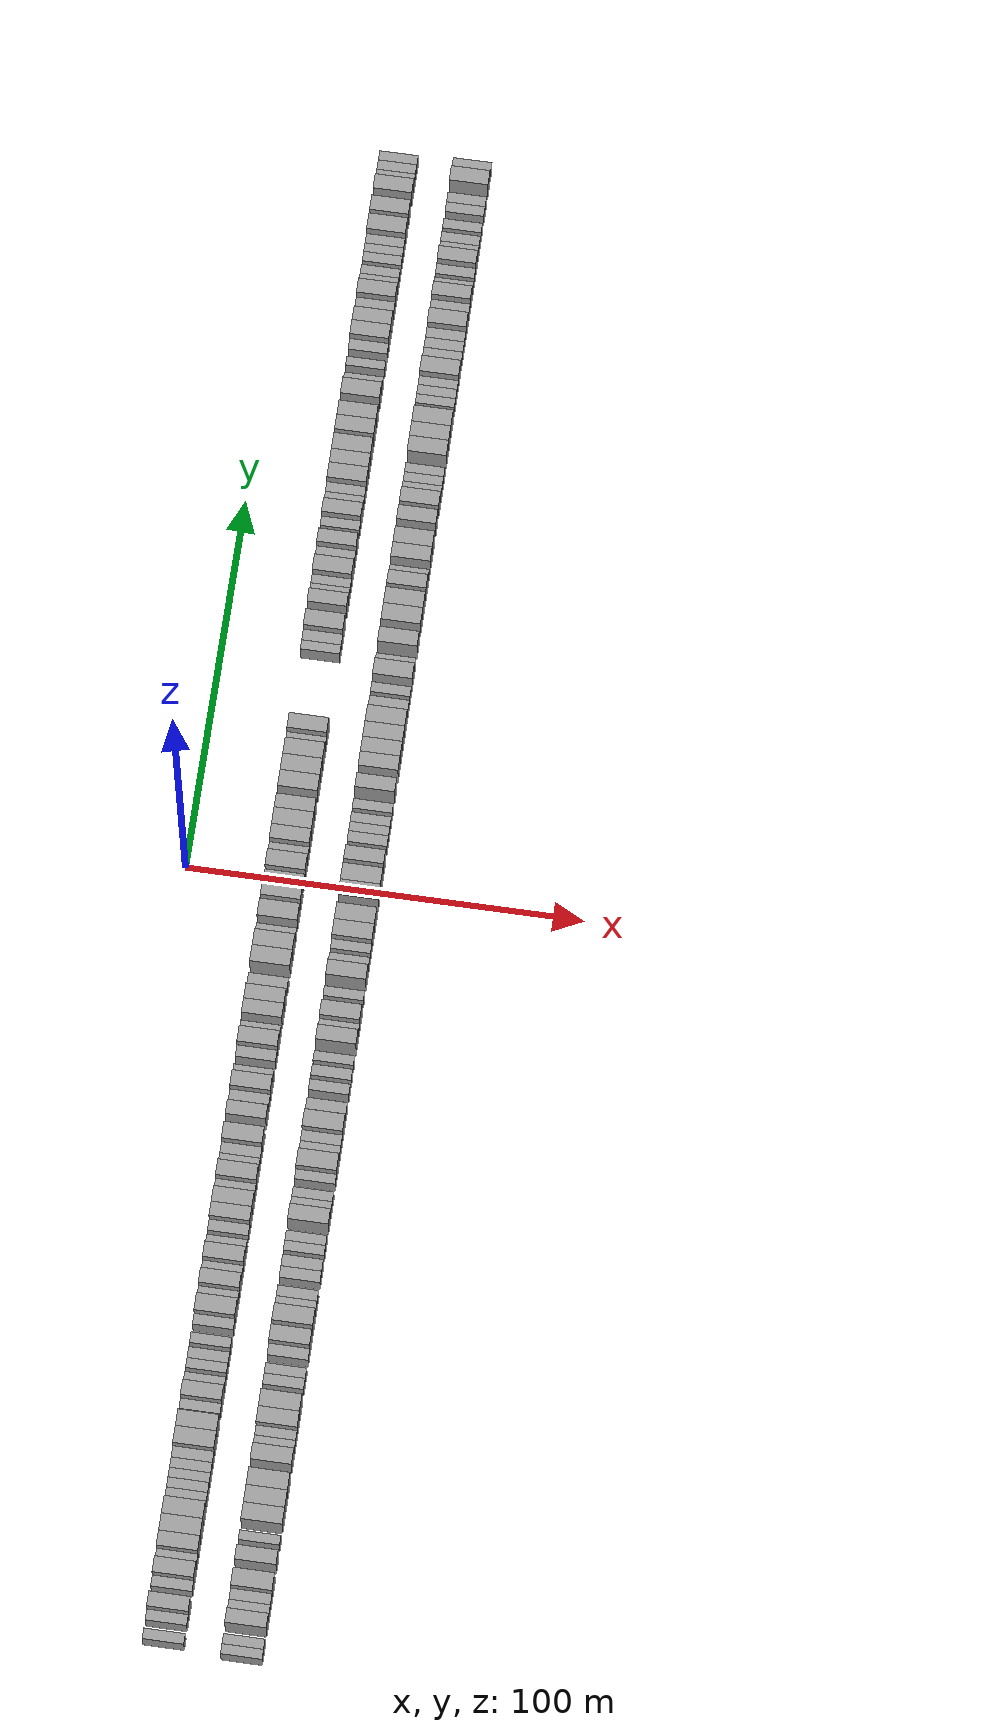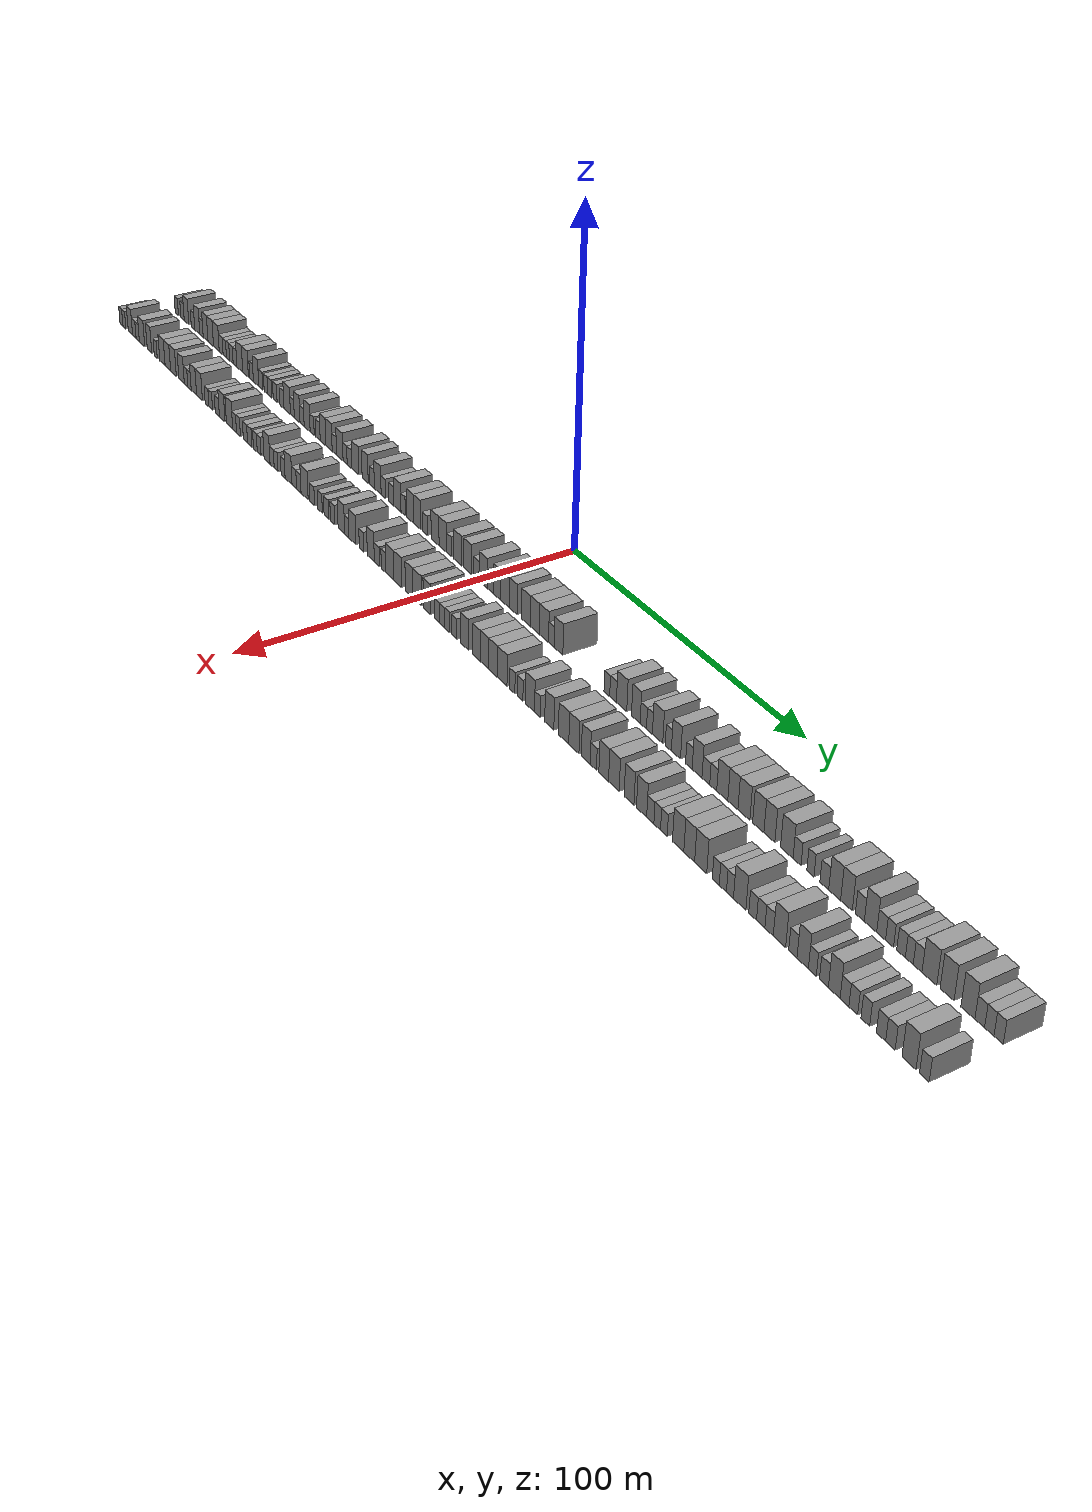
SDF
<sdf version="1.6">
 <world name="default">
  <scene>
   <sky><clouds><speed>12</speed></clouds></sky>
   <ambient>0.4 0.4 0.4 1</ambient>
   <background>0.7 0.7 0.7 1</background>
   <shadows>1</shadows>
  </scene>
  <gravity>0 0 -9.8066</gravity>
  <magnetic_field>6e-06 2.3e-05 -4.2e-05</magnetic_field>
  <physics default="0" name="default_physics" type="ode">
   <ode>
    <solver>
     <type>quick</type>
     <iters>10</iters>
     <sor>1.0</sor>
     <use_dynamic_moi_rescaling>0</use_dynamic_moi_rescaling>
    </solver>
    <constraints>
     <cfm>0</cfm>
     <erp>0.2</erp>
     <contact_max_correcting_vel>100</contact_max_correcting_vel>
     <contact_surface_layer>0.001</contact_surface_layer>
    </constraints>
   </ode>
   <max_step_size>0.004</max_step_size>
   <real_time_factor>1</real_time_factor>
   <real_time_update_rate>250</real_time_update_rate>
  </physics>
  <light name="sun" type="directional">
   <pose>0 0 10 0 0 0</pose>
   <diffuse>0.8 0.8 0.8 1</diffuse>
   <specular>0.2 0.2 0.2 1</specular>
   <attenuation>
    <range>1000</range>
    <constant>0.9</constant>
    <linear>0.01</linear>
    <quadratic>0.001</quadratic>
   </attenuation>
   <direction>-0.5 0.1 -0.9</direction>
  </light>
  <model name="building_1">
   <static>1</static>
   <pose>25.0000 -195.6817 0 0.000000 0.000000 0.000000</pose>
   <link name="link">
    <pose>0 0 3.00 0 0 0</pose>
    <collision name="collision"><geometry><box><size>10.0000 2.6366 6.0000</size></box></geometry></collision>
    <visual name="visual">
     <cast_shadows>0</cast_shadows>
     <geometry><box><size>10.0000 2.6366 6.0000</size></box></geometry>
     <material>
      <script>
       <uri>model://grey_wall/materials/scripts</uri>
       <uri>model://grey_wall/materials/textures</uri>
       <name>vrc/grey_wall</name>
      </script>
     </material>
    </visual>
   </link>
  </model>
  <model name="building_2">
   <static>1</static>
   <pose>25.0000 -191.0178 0 0.000000 0.000000 0.000000</pose>
   <link name="link">
    <pose>0 0 3.00 0 0 0</pose>
    <collision name="collision"><geometry><box><size>10.0000 2.6912 6.0000</size></box></geometry></collision>
    <visual name="visual">
     <cast_shadows>0</cast_shadows>
     <geometry><box><size>10.0000 2.6912 6.0000</size></box></geometry>
     <material>
      <script>
       <uri>model://grey_wall/materials/scripts</uri>
       <uri>model://grey_wall/materials/textures</uri>
       <name>vrc/grey_wall</name>
      </script>
     </material>
    </visual>
   </link>
  </model>
  <model name="building_3">
   <static>1</static>
   <pose>25.0000 -187.8181 0 0.000000 0.000000 0.000000</pose>
   <link name="link">
    <pose>0 0 4.50 0 0 0</pose>
    <collision name="collision"><geometry><box><size>10.0000 3.7082 9.0000</size></box></geometry></collision>
    <visual name="visual">
     <cast_shadows>0</cast_shadows>
     <geometry><box><size>10.0000 3.7082 9.0000</size></box></geometry>
     <material>
      <script>
       <uri>model://grey_wall/materials/scripts</uri>
       <uri>model://grey_wall/materials/textures</uri>
       <name>vrc/grey_wall</name>
      </script>
     </material>
    </visual>
   </link>
  </model>
  <model name="building_4">
   <static>1</static>
   <pose>25.0000 -182.5960 0 0.000000 0.000000 0.000000</pose>
   <link name="link">
    <pose>0 0 3.00 0 0 0</pose>
    <collision name="collision"><geometry><box><size>10.0000 2.7359 6.0000</size></box></geometry></collision>
    <visual name="visual">
     <cast_shadows>0</cast_shadows>
     <geometry><box><size>10.0000 2.7359 6.0000</size></box></geometry>
     <material>
      <script>
       <uri>model://grey_wall/materials/scripts</uri>
       <uri>model://grey_wall/materials/textures</uri>
       <name>vrc/grey_wall</name>
      </script>
     </material>
    </visual>
   </link>
  </model>
  <model name="building_5">
   <static>1</static>
   <pose>25.0000 -179.2441 0 0.000000 0.000000 0.000000</pose>
   <link name="link">
    <pose>0 0 4.50 0 0 0</pose>
    <collision name="collision"><geometry><box><size>10.0000 3.9679 9.0000</size></box></geometry></collision>
    <visual name="visual">
     <cast_shadows>0</cast_shadows>
     <geometry><box><size>10.0000 3.9679 9.0000</size></box></geometry>
     <material>
      <script>
       <uri>model://grey_wall/materials/scripts</uri>
       <uri>model://grey_wall/materials/textures</uri>
       <name>vrc/grey_wall</name>
      </script>
     </material>
    </visual>
   </link>
  </model>
  <model name="building_6">
   <static>1</static>
   <pose>25.0000 -175.9373 0 0.000000 0.000000 0.000000</pose>
   <link name="link">
    <pose>0 0 3.00 0 0 0</pose>
    <collision name="collision"><geometry><box><size>10.0000 2.6457 6.0000</size></box></geometry></collision>
    <visual name="visual">
     <cast_shadows>0</cast_shadows>
     <geometry><box><size>10.0000 2.6457 6.0000</size></box></geometry>
     <material>
      <script>
       <uri>model://grey_wall/materials/scripts</uri>
       <uri>model://grey_wall/materials/textures</uri>
       <name>vrc/grey_wall</name>
      </script>
     </material>
    </visual>
   </link>
  </model>
  <model name="building_7">
   <static>1</static>
   <pose>25.0000 -172.7317 0 0.000000 0.000000 0.000000</pose>
   <link name="link">
    <pose>0 0 4.50 0 0 0</pose>
    <collision name="collision"><geometry><box><size>10.0000 3.7654 9.0000</size></box></geometry></collision>
    <visual name="visual">
     <cast_shadows>0</cast_shadows>
     <geometry><box><size>10.0000 3.7654 9.0000</size></box></geometry>
     <material>
      <script>
       <uri>model://grey_wall/materials/scripts</uri>
       <uri>model://grey_wall/materials/textures</uri>
       <name>vrc/grey_wall</name>
      </script>
     </material>
    </visual>
   </link>
  </model>
  <model name="building_8">
   <static>1</static>
   <pose>25.0000 -168.7135 0 0.000000 0.000000 0.000000</pose>
   <link name="link">
    <pose>0 0 4.50 0 0 0</pose>
    <collision name="collision"><geometry><box><size>10.0000 4.2710 9.0000</size></box></geometry></collision>
    <visual name="visual">
     <cast_shadows>0</cast_shadows>
     <geometry><box><size>10.0000 4.2710 9.0000</size></box></geometry>
     <material>
      <script>
       <uri>model://grey_wall/materials/scripts</uri>
       <uri>model://grey_wall/materials/textures</uri>
       <name>vrc/grey_wall</name>
      </script>
     </material>
    </visual>
   </link>
  </model>
  <model name="building_9">
   <static>1</static>
   <pose>25.0000 -164.4057 0 0.000000 0.000000 0.000000</pose>
   <link name="link">
    <pose>0 0 4.50 0 0 0</pose>
    <collision name="collision"><geometry><box><size>10.0000 4.3447 9.0000</size></box></geometry></collision>
    <visual name="visual">
     <cast_shadows>0</cast_shadows>
     <geometry><box><size>10.0000 4.3447 9.0000</size></box></geometry>
     <material>
      <script>
       <uri>model://grey_wall/materials/scripts</uri>
       <uri>model://grey_wall/materials/textures</uri>
       <name>vrc/grey_wall</name>
      </script>
     </material>
    </visual>
   </link>
  </model>
  <model name="building_10">
   <static>1</static>
   <pose>25.0000 -160.7560 0 0.000000 0.000000 0.000000</pose>
   <link name="link">
    <pose>0 0 3.00 0 0 0</pose>
    <collision name="collision"><geometry><box><size>10.0000 2.9547 6.0000</size></box></geometry></collision>
    <visual name="visual">
     <cast_shadows>0</cast_shadows>
     <geometry><box><size>10.0000 2.9547 6.0000</size></box></geometry>
     <material>
      <script>
       <uri>model://grey_wall/materials/scripts</uri>
       <uri>model://grey_wall/materials/textures</uri>
       <name>vrc/grey_wall</name>
      </script>
     </material>
    </visual>
   </link>
  </model>
  <model name="building_11">
   <static>1</static>
   <pose>25.0000 -158.0218 0 0.000000 0.000000 0.000000</pose>
   <link name="link">
    <pose>0 0 3.00 0 0 0</pose>
    <collision name="collision"><geometry><box><size>10.0000 2.5139 6.0000</size></box></geometry></collision>
    <visual name="visual">
     <cast_shadows>0</cast_shadows>
     <geometry><box><size>10.0000 2.5139 6.0000</size></box></geometry>
     <material>
      <script>
       <uri>model://grey_wall/materials/scripts</uri>
       <uri>model://grey_wall/materials/textures</uri>
       <name>vrc/grey_wall</name>
      </script>
     </material>
    </visual>
   </link>
  </model>
  <model name="building_12">
   <static>1</static>
   <pose>25.0000 -155.5524 0 0.000000 0.000000 0.000000</pose>
   <link name="link">
    <pose>0 0 3.00 0 0 0</pose>
    <collision name="collision"><geometry><box><size>10.0000 2.4248 6.0000</size></box></geometry></collision>
    <visual name="visual">
     <cast_shadows>0</cast_shadows>
     <geometry><box><size>10.0000 2.4248 6.0000</size></box></geometry>
     <material>
      <script>
       <uri>model://grey_wall/materials/scripts</uri>
       <uri>model://grey_wall/materials/textures</uri>
       <name>vrc/grey_wall</name>
      </script>
     </material>
    </visual>
   </link>
  </model>
  <model name="building_13">
   <static>1</static>
   <pose>25.0000 -153.0496 0 0.000000 0.000000 0.000000</pose>
   <link name="link">
    <pose>0 0 3.00 0 0 0</pose>
    <collision name="collision"><geometry><box><size>10.0000 2.5808 6.0000</size></box></geometry></collision>
    <visual name="visual">
     <cast_shadows>0</cast_shadows>
     <geometry><box><size>10.0000 2.5808 6.0000</size></box></geometry>
     <material>
      <script>
       <uri>model://grey_wall/materials/scripts</uri>
       <uri>model://grey_wall/materials/textures</uri>
       <name>vrc/grey_wall</name>
      </script>
     </material>
    </visual>
   </link>
  </model>
  <model name="building_14">
   <static>1</static>
   <pose>25.0000 -150.3608 0 0.000000 0.000000 0.000000</pose>
   <link name="link">
    <pose>0 0 3.00 0 0 0</pose>
    <collision name="collision"><geometry><box><size>10.0000 2.7970 6.0000</size></box></geometry></collision>
    <visual name="visual">
     <cast_shadows>0</cast_shadows>
     <geometry><box><size>10.0000 2.7970 6.0000</size></box></geometry>
     <material>
      <script>
       <uri>model://grey_wall/materials/scripts</uri>
       <uri>model://grey_wall/materials/textures</uri>
       <name>vrc/grey_wall</name>
      </script>
     </material>
    </visual>
   </link>
  </model>
  <model name="building_15">
   <static>1</static>
   <pose>25.0000 -146.8116 0 0.000000 0.000000 0.000000</pose>
   <link name="link">
    <pose>0 0 4.50 0 0 0</pose>
    <collision name="collision"><geometry><box><size>10.0000 4.3014 9.0000</size></box></geometry></collision>
    <visual name="visual">
     <cast_shadows>0</cast_shadows>
     <geometry><box><size>10.0000 4.3014 9.0000</size></box></geometry>
     <material>
      <script>
       <uri>model://grey_wall/materials/scripts</uri>
       <uri>model://grey_wall/materials/textures</uri>
       <name>vrc/grey_wall</name>
      </script>
     </material>
    </visual>
   </link>
  </model>
  <model name="building_16">
   <static>1</static>
   <pose>25.0000 -142.6003 0 0.000000 0.000000 0.000000</pose>
   <link name="link">
    <pose>0 0 4.50 0 0 0</pose>
    <collision name="collision"><geometry><box><size>10.0000 4.1212 9.0000</size></box></geometry></collision>
    <visual name="visual">
     <cast_shadows>0</cast_shadows>
     <geometry><box><size>10.0000 4.1212 9.0000</size></box></geometry>
     <material>
      <script>
       <uri>model://grey_wall/materials/scripts</uri>
       <uri>model://grey_wall/materials/textures</uri>
       <name>vrc/grey_wall</name>
      </script>
     </material>
    </visual>
   </link>
  </model>
  <model name="building_17">
   <static>1</static>
   <pose>25.0000 -138.2279 0 0.000000 0.000000 0.000000</pose>
   <link name="link">
    <pose>0 0 3.00 0 0 0</pose>
    <collision name="collision"><geometry><box><size>10.0000 2.6235 6.0000</size></box></geometry></collision>
    <visual name="visual">
     <cast_shadows>0</cast_shadows>
     <geometry><box><size>10.0000 2.6235 6.0000</size></box></geometry>
     <material>
      <script>
       <uri>model://grey_wall/materials/scripts</uri>
       <uri>model://grey_wall/materials/textures</uri>
       <name>vrc/grey_wall</name>
      </script>
     </material>
    </visual>
   </link>
  </model>
  <model name="building_18">
   <static>1</static>
   <pose>25.0000 -134.9828 0 0.000000 0.000000 0.000000</pose>
   <link name="link">
    <pose>0 0 4.50 0 0 0</pose>
    <collision name="collision"><geometry><box><size>10.0000 3.8667 9.0000</size></box></geometry></collision>
    <visual name="visual">
     <cast_shadows>0</cast_shadows>
     <geometry><box><size>10.0000 3.8667 9.0000</size></box></geometry>
     <material>
      <script>
       <uri>model://grey_wall/materials/scripts</uri>
       <uri>model://grey_wall/materials/textures</uri>
       <name>vrc/grey_wall</name>
      </script>
     </material>
    </visual>
   </link>
  </model>
  <model name="building_19">
   <static>1</static>
   <pose>25.0000 -131.6257 0 0.000000 0.000000 0.000000</pose>
   <link name="link">
    <pose>0 0 3.00 0 0 0</pose>
    <collision name="collision"><geometry><box><size>10.0000 2.8475 6.0000</size></box></geometry></collision>
    <visual name="visual">
     <cast_shadows>0</cast_shadows>
     <geometry><box><size>10.0000 2.8475 6.0000</size></box></geometry>
     <material>
      <script>
       <uri>model://grey_wall/materials/scripts</uri>
       <uri>model://grey_wall/materials/textures</uri>
       <name>vrc/grey_wall</name>
      </script>
     </material>
    </visual>
   </link>
  </model>
  <model name="building_20">
   <static>1</static>
   <pose>25.0000 -127.9297 0 0.000000 0.000000 0.000000</pose>
   <link name="link">
    <pose>0 0 3.00 0 0 0</pose>
    <collision name="collision"><geometry><box><size>10.0000 2.5444 6.0000</size></box></geometry></collision>
    <visual name="visual">
     <cast_shadows>0</cast_shadows>
     <geometry><box><size>10.0000 2.5444 6.0000</size></box></geometry>
     <material>
      <script>
       <uri>model://grey_wall/materials/scripts</uri>
       <uri>model://grey_wall/materials/textures</uri>
       <name>vrc/grey_wall</name>
      </script>
     </material>
    </visual>
   </link>
  </model>
  <model name="building_21">
   <static>1</static>
   <pose>25.0000 -125.2674 0 0.000000 0.000000 0.000000</pose>
   <link name="link">
    <pose>0 0 3.00 0 0 0</pose>
    <collision name="collision"><geometry><box><size>10.0000 2.7802 6.0000</size></box></geometry></collision>
    <visual name="visual">
     <cast_shadows>0</cast_shadows>
     <geometry><box><size>10.0000 2.7802 6.0000</size></box></geometry>
     <material>
      <script>
       <uri>model://grey_wall/materials/scripts</uri>
       <uri>model://grey_wall/materials/textures</uri>
       <name>vrc/grey_wall</name>
      </script>
     </material>
    </visual>
   </link>
  </model>
  <model name="building_22">
   <static>1</static>
   <pose>25.0000 -121.5234 0 0.000000 0.000000 0.000000</pose>
   <link name="link">
    <pose>0 0 3.00 0 0 0</pose>
    <collision name="collision"><geometry><box><size>10.0000 2.7080 6.0000</size></box></geometry></collision>
    <visual name="visual">
     <cast_shadows>0</cast_shadows>
     <geometry><box><size>10.0000 2.7080 6.0000</size></box></geometry>
     <material>
      <script>
       <uri>model://grey_wall/materials/scripts</uri>
       <uri>model://grey_wall/materials/textures</uri>
       <name>vrc/grey_wall</name>
      </script>
     </material>
    </visual>
   </link>
  </model>
  <model name="building_23">
   <static>1</static>
   <pose>25.0000 -116.7944 0 0.000000 0.000000 0.000000</pose>
   <link name="link">
    <pose>0 0 3.00 0 0 0</pose>
    <collision name="collision"><geometry><box><size>10.0000 2.7501 6.0000</size></box></geometry></collision>
    <visual name="visual">
     <cast_shadows>0</cast_shadows>
     <geometry><box><size>10.0000 2.7501 6.0000</size></box></geometry>
     <material>
      <script>
       <uri>model://grey_wall/materials/scripts</uri>
       <uri>model://grey_wall/materials/textures</uri>
       <name>vrc/grey_wall</name>
      </script>
     </material>
    </visual>
   </link>
  </model>
  <model name="building_24">
   <static>1</static>
   <pose>25.0000 -113.2171 0 0.000000 0.000000 0.000000</pose>
   <link name="link">
    <pose>0 0 4.50 0 0 0</pose>
    <collision name="collision"><geometry><box><size>10.0000 4.4045 9.0000</size></box></geometry></collision>
    <visual name="visual">
     <cast_shadows>0</cast_shadows>
     <geometry><box><size>10.0000 4.4045 9.0000</size></box></geometry>
     <material>
      <script>
       <uri>model://grey_wall/materials/scripts</uri>
       <uri>model://grey_wall/materials/textures</uri>
       <name>vrc/grey_wall</name>
      </script>
     </material>
    </visual>
   </link>
  </model>
  <model name="building_25">
   <static>1</static>
   <pose>25.0000 -109.7025 0 0.000000 0.000000 0.000000</pose>
   <link name="link">
    <pose>0 0 3.00 0 0 0</pose>
    <collision name="collision"><geometry><box><size>10.0000 2.6247 6.0000</size></box></geometry></collision>
    <visual name="visual">
     <cast_shadows>0</cast_shadows>
     <geometry><box><size>10.0000 2.6247 6.0000</size></box></geometry>
     <material>
      <script>
       <uri>model://grey_wall/materials/scripts</uri>
       <uri>model://grey_wall/materials/textures</uri>
       <name>vrc/grey_wall</name>
      </script>
     </material>
    </visual>
   </link>
  </model>
  <model name="building_26">
   <static>1</static>
   <pose>25.0000 -106.4884 0 0.000000 0.000000 0.000000</pose>
   <link name="link">
    <pose>0 0 4.50 0 0 0</pose>
    <collision name="collision"><geometry><box><size>10.0000 3.8035 9.0000</size></box></geometry></collision>
    <visual name="visual">
     <cast_shadows>0</cast_shadows>
     <geometry><box><size>10.0000 3.8035 9.0000</size></box></geometry>
     <material>
      <script>
       <uri>model://grey_wall/materials/scripts</uri>
       <uri>model://grey_wall/materials/textures</uri>
       <name>vrc/grey_wall</name>
      </script>
     </material>
    </visual>
   </link>
  </model>
  <model name="building_27">
   <static>1</static>
   <pose>25.0000 -103.1999 0 0.000000 0.000000 0.000000</pose>
   <link name="link">
    <pose>0 0 3.00 0 0 0</pose>
    <collision name="collision"><geometry><box><size>10.0000 2.7735 6.0000</size></box></geometry></collision>
    <visual name="visual">
     <cast_shadows>0</cast_shadows>
     <geometry><box><size>10.0000 2.7735 6.0000</size></box></geometry>
     <material>
      <script>
       <uri>model://grey_wall/materials/scripts</uri>
       <uri>model://grey_wall/materials/textures</uri>
       <name>vrc/grey_wall</name>
      </script>
     </material>
    </visual>
   </link>
  </model>
  <model name="building_28">
   <static>1</static>
   <pose>25.0000 -99.8397 0 0.000000 0.000000 0.000000</pose>
   <link name="link">
    <pose>0 0 4.50 0 0 0</pose>
    <collision name="collision"><geometry><box><size>10.0000 3.9468 9.0000</size></box></geometry></collision>
    <visual name="visual">
     <cast_shadows>0</cast_shadows>
     <geometry><box><size>10.0000 3.9468 9.0000</size></box></geometry>
     <material>
      <script>
       <uri>model://grey_wall/materials/scripts</uri>
       <uri>model://grey_wall/materials/textures</uri>
       <name>vrc/grey_wall</name>
      </script>
     </material>
    </visual>
   </link>
  </model>
  <model name="building_29">
   <static>1</static>
   <pose>25.0000 -96.5197 0 0.000000 0.000000 0.000000</pose>
   <link name="link">
    <pose>0 0 3.00 0 0 0</pose>
    <collision name="collision"><geometry><box><size>10.0000 2.6931 6.0000</size></box></geometry></collision>
    <visual name="visual">
     <cast_shadows>0</cast_shadows>
     <geometry><box><size>10.0000 2.6931 6.0000</size></box></geometry>
     <material>
      <script>
       <uri>model://grey_wall/materials/scripts</uri>
       <uri>model://grey_wall/materials/textures</uri>
       <name>vrc/grey_wall</name>
      </script>
     </material>
    </visual>
   </link>
  </model>
  <model name="building_30">
   <static>1</static>
   <pose>25.0000 -92.7318 0 0.000000 0.000000 0.000000</pose>
   <link name="link">
    <pose>0 0 3.00 0 0 0</pose>
    <collision name="collision"><geometry><box><size>10.0000 2.8827 6.0000</size></box></geometry></collision>
    <visual name="visual">
     <cast_shadows>0</cast_shadows>
     <geometry><box><size>10.0000 2.8827 6.0000</size></box></geometry>
     <material>
      <script>
       <uri>model://grey_wall/materials/scripts</uri>
       <uri>model://grey_wall/materials/textures</uri>
       <name>vrc/grey_wall</name>
      </script>
     </material>
    </visual>
   </link>
  </model>
  <model name="building_31">
   <static>1</static>
   <pose>25.0000 -89.4552 0 0.000000 0.000000 0.000000</pose>
   <link name="link">
    <pose>0 0 4.50 0 0 0</pose>
    <collision name="collision"><geometry><box><size>10.0000 3.6705 9.0000</size></box></geometry></collision>
    <visual name="visual">
     <cast_shadows>0</cast_shadows>
     <geometry><box><size>10.0000 3.6705 9.0000</size></box></geometry>
     <material>
      <script>
       <uri>model://grey_wall/materials/scripts</uri>
       <uri>model://grey_wall/materials/textures</uri>
       <name>vrc/grey_wall</name>
      </script>
     </material>
    </visual>
   </link>
  </model>
  <model name="building_32">
   <static>1</static>
   <pose>25.0000 -85.6126 0 0.000000 0.000000 0.000000</pose>
   <link name="link">
    <pose>0 0 4.50 0 0 0</pose>
    <collision name="collision"><geometry><box><size>10.0000 4.0149 9.0000</size></box></geometry></collision>
    <visual name="visual">
     <cast_shadows>0</cast_shadows>
     <geometry><box><size>10.0000 4.0149 9.0000</size></box></geometry>
     <material>
      <script>
       <uri>model://grey_wall/materials/scripts</uri>
       <uri>model://grey_wall/materials/textures</uri>
       <name>vrc/grey_wall</name>
      </script>
     </material>
    </visual>
   </link>
  </model>
  <model name="building_33">
   <static>1</static>
   <pose>25.0000 -82.1980 0 0.000000 0.000000 0.000000</pose>
   <link name="link">
    <pose>0 0 3.00 0 0 0</pose>
    <collision name="collision"><geometry><box><size>10.0000 2.8143 6.0000</size></box></geometry></collision>
    <visual name="visual">
     <cast_shadows>0</cast_shadows>
     <geometry><box><size>10.0000 2.8143 6.0000</size></box></geometry>
     <material>
      <script>
       <uri>model://grey_wall/materials/scripts</uri>
       <uri>model://grey_wall/materials/textures</uri>
       <name>vrc/grey_wall</name>
      </script>
     </material>
    </visual>
   </link>
  </model>
  <model name="building_34">
   <static>1</static>
   <pose>25.0000 -78.7578 0 0.000000 0.000000 0.000000</pose>
   <link name="link">
    <pose>0 0 4.50 0 0 0</pose>
    <collision name="collision"><geometry><box><size>10.0000 4.0661 9.0000</size></box></geometry></collision>
    <visual name="visual">
     <cast_shadows>0</cast_shadows>
     <geometry><box><size>10.0000 4.0661 9.0000</size></box></geometry>
     <material>
      <script>
       <uri>model://grey_wall/materials/scripts</uri>
       <uri>model://grey_wall/materials/textures</uri>
       <name>vrc/grey_wall</name>
      </script>
     </material>
    </visual>
   </link>
  </model>
  <model name="building_35">
   <static>1</static>
   <pose>25.0000 -75.4524 0 0.000000 0.000000 0.000000</pose>
   <link name="link">
    <pose>0 0 3.00 0 0 0</pose>
    <collision name="collision"><geometry><box><size>10.0000 2.5446 6.0000</size></box></geometry></collision>
    <visual name="visual">
     <cast_shadows>0</cast_shadows>
     <geometry><box><size>10.0000 2.5446 6.0000</size></box></geometry>
     <material>
      <script>
       <uri>model://grey_wall/materials/scripts</uri>
       <uri>model://grey_wall/materials/textures</uri>
       <name>vrc/grey_wall</name>
      </script>
     </material>
    </visual>
   </link>
  </model>
  <model name="building_36">
   <static>1</static>
   <pose>25.0000 -72.7399 0 0.000000 0.000000 0.000000</pose>
   <link name="link">
    <pose>0 0 3.00 0 0 0</pose>
    <collision name="collision"><geometry><box><size>10.0000 2.8805 6.0000</size></box></geometry></collision>
    <visual name="visual">
     <cast_shadows>0</cast_shadows>
     <geometry><box><size>10.0000 2.8805 6.0000</size></box></geometry>
     <material>
      <script>
       <uri>model://grey_wall/materials/scripts</uri>
       <uri>model://grey_wall/materials/textures</uri>
       <name>vrc/grey_wall</name>
      </script>
     </material>
    </visual>
   </link>
  </model>
  <model name="building_37">
   <static>1</static>
   <pose>25.0000 -69.1402 0 0.000000 0.000000 0.000000</pose>
   <link name="link">
    <pose>0 0 4.50 0 0 0</pose>
    <collision name="collision"><geometry><box><size>10.0000 4.3190 9.0000</size></box></geometry></collision>
    <visual name="visual">
     <cast_shadows>0</cast_shadows>
     <geometry><box><size>10.0000 4.3190 9.0000</size></box></geometry>
     <material>
      <script>
       <uri>model://grey_wall/materials/scripts</uri>
       <uri>model://grey_wall/materials/textures</uri>
       <name>vrc/grey_wall</name>
      </script>
     </material>
    </visual>
   </link>
  </model>
  <model name="building_38">
   <static>1</static>
   <pose>25.0000 -63.1433 0 0.000000 0.000000 0.000000</pose>
   <link name="link">
    <pose>0 0 4.50 0 0 0</pose>
    <collision name="collision"><geometry><box><size>10.0000 3.6747 9.0000</size></box></geometry></collision>
    <visual name="visual">
     <cast_shadows>0</cast_shadows>
     <geometry><box><size>10.0000 3.6747 9.0000</size></box></geometry>
     <material>
      <script>
       <uri>model://grey_wall/materials/scripts</uri>
       <uri>model://grey_wall/materials/textures</uri>
       <name>vrc/grey_wall</name>
      </script>
     </material>
    </visual>
   </link>
  </model>
  <model name="building_39">
   <static>1</static>
   <pose>25.0000 -58.9507 0 0.000000 0.000000 0.000000</pose>
   <link name="link">
    <pose>0 0 3.00 0 0 0</pose>
    <collision name="collision"><geometry><box><size>10.0000 2.7105 6.0000</size></box></geometry></collision>
    <visual name="visual">
     <cast_shadows>0</cast_shadows>
     <geometry><box><size>10.0000 2.7105 6.0000</size></box></geometry>
     <material>
      <script>
       <uri>model://grey_wall/materials/scripts</uri>
       <uri>model://grey_wall/materials/textures</uri>
       <name>vrc/grey_wall</name>
      </script>
     </material>
    </visual>
   </link>
  </model>
  <model name="building_40">
   <static>1</static>
   <pose>25.0000 -55.5924 0 0.000000 0.000000 0.000000</pose>
   <link name="link">
    <pose>0 0 4.50 0 0 0</pose>
    <collision name="collision"><geometry><box><size>10.0000 4.0061 9.0000</size></box></geometry></collision>
    <visual name="visual">
     <cast_shadows>0</cast_shadows>
     <geometry><box><size>10.0000 4.0061 9.0000</size></box></geometry>
     <material>
      <script>
       <uri>model://grey_wall/materials/scripts</uri>
       <uri>model://grey_wall/materials/textures</uri>
       <name>vrc/grey_wall</name>
      </script>
     </material>
    </visual>
   </link>
  </model>
  <model name="building_41">
   <static>1</static>
   <pose>25.0000 -52.3257 0 0.000000 0.000000 0.000000</pose>
   <link name="link">
    <pose>0 0 3.00 0 0 0</pose>
    <collision name="collision"><geometry><box><size>10.0000 2.5272 6.0000</size></box></geometry></collision>
    <visual name="visual">
     <cast_shadows>0</cast_shadows>
     <geometry><box><size>10.0000 2.5272 6.0000</size></box></geometry>
     <material>
      <script>
       <uri>model://grey_wall/materials/scripts</uri>
       <uri>model://grey_wall/materials/textures</uri>
       <name>vrc/grey_wall</name>
      </script>
     </material>
    </visual>
   </link>
  </model>
  <model name="building_42">
   <static>1</static>
   <pose>25.0000 -47.5764 0 0.000000 0.000000 0.000000</pose>
   <link name="link">
    <pose>0 0 3.00 0 0 0</pose>
    <collision name="collision"><geometry><box><size>10.0000 2.9714 6.0000</size></box></geometry></collision>
    <visual name="visual">
     <cast_shadows>0</cast_shadows>
     <geometry><box><size>10.0000 2.9714 6.0000</size></box></geometry>
     <material>
      <script>
       <uri>model://grey_wall/materials/scripts</uri>
       <uri>model://grey_wall/materials/textures</uri>
       <name>vrc/grey_wall</name>
      </script>
     </material>
    </visual>
   </link>
  </model>
  <model name="building_43">
   <static>1</static>
   <pose>25.0000 -44.0387 0 0.000000 0.000000 0.000000</pose>
   <link name="link">
    <pose>0 0 4.50 0 0 0</pose>
    <collision name="collision"><geometry><box><size>10.0000 4.1039 9.0000</size></box></geometry></collision>
    <visual name="visual">
     <cast_shadows>0</cast_shadows>
     <geometry><box><size>10.0000 4.1039 9.0000</size></box></geometry>
     <material>
      <script>
       <uri>model://grey_wall/materials/scripts</uri>
       <uri>model://grey_wall/materials/textures</uri>
       <name>vrc/grey_wall</name>
      </script>
     </material>
    </visual>
   </link>
  </model>
  <model name="building_44">
   <static>1</static>
   <pose>25.0000 -40.7745 0 0.000000 0.000000 0.000000</pose>
   <link name="link">
    <pose>0 0 3.00 0 0 0</pose>
    <collision name="collision"><geometry><box><size>10.0000 2.4245 6.0000</size></box></geometry></collision>
    <visual name="visual">
     <cast_shadows>0</cast_shadows>
     <geometry><box><size>10.0000 2.4245 6.0000</size></box></geometry>
     <material>
      <script>
       <uri>model://grey_wall/materials/scripts</uri>
       <uri>model://grey_wall/materials/textures</uri>
       <name>vrc/grey_wall</name>
      </script>
     </material>
    </visual>
   </link>
  </model>
  <model name="building_45">
   <static>1</static>
   <pose>25.0000 -36.6715 0 0.000000 0.000000 0.000000</pose>
   <link name="link">
    <pose>0 0 4.50 0 0 0</pose>
    <collision name="collision"><geometry><box><size>10.0000 3.7815 9.0000</size></box></geometry></collision>
    <visual name="visual">
     <cast_shadows>0</cast_shadows>
     <geometry><box><size>10.0000 3.7815 9.0000</size></box></geometry>
     <material>
      <script>
       <uri>model://grey_wall/materials/scripts</uri>
       <uri>model://grey_wall/materials/textures</uri>
       <name>vrc/grey_wall</name>
      </script>
     </material>
    </visual>
   </link>
  </model>
  <model name="building_46">
   <static>1</static>
   <pose>25.0000 -32.8345 0 0.000000 0.000000 0.000000</pose>
   <link name="link">
    <pose>0 0 4.50 0 0 0</pose>
    <collision name="collision"><geometry><box><size>10.0000 3.8925 9.0000</size></box></geometry></collision>
    <visual name="visual">
     <cast_shadows>0</cast_shadows>
     <geometry><box><size>10.0000 3.8925 9.0000</size></box></geometry>
     <material>
      <script>
       <uri>model://grey_wall/materials/scripts</uri>
       <uri>model://grey_wall/materials/textures</uri>
       <name>vrc/grey_wall</name>
      </script>
     </material>
    </visual>
   </link>
  </model>
  <model name="building_47">
   <static>1</static>
   <pose>25.0000 -28.4580 0 0.000000 0.000000 0.000000</pose>
   <link name="link">
    <pose>0 0 3.00 0 0 0</pose>
    <collision name="collision"><geometry><box><size>10.0000 2.8605 6.0000</size></box></geometry></collision>
    <visual name="visual">
     <cast_shadows>0</cast_shadows>
     <geometry><box><size>10.0000 2.8605 6.0000</size></box></geometry>
     <material>
      <script>
       <uri>model://grey_wall/materials/scripts</uri>
       <uri>model://grey_wall/materials/textures</uri>
       <name>vrc/grey_wall</name>
      </script>
     </material>
    </visual>
   </link>
  </model>
  <model name="building_48">
   <static>1</static>
   <pose>25.0000 -22.8673 0 0.000000 0.000000 0.000000</pose>
   <link name="link">
    <pose>0 0 4.50 0 0 0</pose>
    <collision name="collision"><geometry><box><size>10.0000 4.3210 9.0000</size></box></geometry></collision>
    <visual name="visual">
     <cast_shadows>0</cast_shadows>
     <geometry><box><size>10.0000 4.3210 9.0000</size></box></geometry>
     <material>
      <script>
       <uri>model://grey_wall/materials/scripts</uri>
       <uri>model://grey_wall/materials/textures</uri>
       <name>vrc/grey_wall</name>
      </script>
     </material>
    </visual>
   </link>
  </model>
  <model name="building_49">
   <static>1</static>
   <pose>25.0000 -18.6075 0 0.000000 0.000000 0.000000</pose>
   <link name="link">
    <pose>0 0 4.50 0 0 0</pose>
    <collision name="collision"><geometry><box><size>10.0000 4.1986 9.0000</size></box></geometry></collision>
    <visual name="visual">
     <cast_shadows>0</cast_shadows>
     <geometry><box><size>10.0000 4.1986 9.0000</size></box></geometry>
     <material>
      <script>
       <uri>model://grey_wall/materials/scripts</uri>
       <uri>model://grey_wall/materials/textures</uri>
       <name>vrc/grey_wall</name>
      </script>
     </material>
    </visual>
   </link>
  </model>
  <model name="building_50">
   <static>1</static>
   <pose>25.0000 -15.2015 0 0.000000 0.000000 0.000000</pose>
   <link name="link">
    <pose>0 0 3.00 0 0 0</pose>
    <collision name="collision"><geometry><box><size>10.0000 2.6134 6.0000</size></box></geometry></collision>
    <visual name="visual">
     <cast_shadows>0</cast_shadows>
     <geometry><box><size>10.0000 2.6134 6.0000</size></box></geometry>
     <material>
      <script>
       <uri>model://grey_wall/materials/scripts</uri>
       <uri>model://grey_wall/materials/textures</uri>
       <name>vrc/grey_wall</name>
      </script>
     </material>
    </visual>
   </link>
  </model>
  <model name="building_51">
   <static>1</static>
   <pose>25.0000 -10.6625 0 0.000000 0.000000 0.000000</pose>
   <link name="link">
    <pose>0 0 4.50 0 0 0</pose>
    <collision name="collision"><geometry><box><size>10.0000 4.4645 9.0000</size></box></geometry></collision>
    <visual name="visual">
     <cast_shadows>0</cast_shadows>
     <geometry><box><size>10.0000 4.4645 9.0000</size></box></geometry>
     <material>
      <script>
       <uri>model://grey_wall/materials/scripts</uri>
       <uri>model://grey_wall/materials/textures</uri>
       <name>vrc/grey_wall</name>
      </script>
     </material>
    </visual>
   </link>
  </model>
  <model name="building_52">
   <static>1</static>
   <pose>25.0000 -5.4707 0 0.000000 0.000000 0.000000</pose>
   <link name="link">
    <pose>0 0 4.50 0 0 0</pose>
    <collision name="collision"><geometry><box><size>10.0000 3.9190 9.0000</size></box></geometry></collision>
    <visual name="visual">
     <cast_shadows>0</cast_shadows>
     <geometry><box><size>10.0000 3.9190 9.0000</size></box></geometry>
     <material>
      <script>
       <uri>model://grey_wall/materials/scripts</uri>
       <uri>model://grey_wall/materials/textures</uri>
       <name>vrc/grey_wall</name>
      </script>
     </material>
    </visual>
   </link>
  </model>
  <model name="building_53">
   <static>1</static>
   <pose>25.0000 -1.0420 0 0.000000 0.000000 0.000000</pose>
   <link name="link">
    <pose>0 0 3.00 0 0 0</pose>
    <collision name="collision"><geometry><box><size>10.0000 2.9385 6.0000</size></box></geometry></collision>
    <visual name="visual">
     <cast_shadows>0</cast_shadows>
     <geometry><box><size>10.0000 2.9385 6.0000</size></box></geometry>
     <material>
      <script>
       <uri>model://grey_wall/materials/scripts</uri>
       <uri>model://grey_wall/materials/textures</uri>
       <name>vrc/grey_wall</name>
      </script>
     </material>
    </visual>
   </link>
  </model>
  <model name="building_54">
   <static>1</static>
   <pose>25.0000 2.5894 0 0.000000 0.000000 0.000000</pose>
   <link name="link">
    <pose>0 0 4.50 0 0 0</pose>
    <collision name="collision"><geometry><box><size>10.0000 4.3243 9.0000</size></box></geometry></collision>
    <visual name="visual">
     <cast_shadows>0</cast_shadows>
     <geometry><box><size>10.0000 4.3243 9.0000</size></box></geometry>
     <material>
      <script>
       <uri>model://grey_wall/materials/scripts</uri>
       <uri>model://grey_wall/materials/textures</uri>
       <name>vrc/grey_wall</name>
      </script>
     </material>
    </visual>
   </link>
  </model>
  <model name="building_55">
   <static>1</static>
   <pose>25.0000 6.2147 0 0.000000 0.000000 0.000000</pose>
   <link name="link">
    <pose>0 0 3.00 0 0 0</pose>
    <collision name="collision"><geometry><box><size>10.0000 2.9261 6.0000</size></box></geometry></collision>
    <visual name="visual">
     <cast_shadows>0</cast_shadows>
     <geometry><box><size>10.0000 2.9261 6.0000</size></box></geometry>
     <material>
      <script>
       <uri>model://grey_wall/materials/scripts</uri>
       <uri>model://grey_wall/materials/textures</uri>
       <name>vrc/grey_wall</name>
      </script>
     </material>
    </visual>
   </link>
  </model>
  <model name="building_56">
   <static>1</static>
   <pose>25.0000 9.5672 0 0.000000 0.000000 0.000000</pose>
   <link name="link">
    <pose>0 0 4.50 0 0 0</pose>
    <collision name="collision"><geometry><box><size>10.0000 3.7789 9.0000</size></box></geometry></collision>
    <visual name="visual">
     <cast_shadows>0</cast_shadows>
     <geometry><box><size>10.0000 3.7789 9.0000</size></box></geometry>
     <material>
      <script>
       <uri>model://grey_wall/materials/scripts</uri>
       <uri>model://grey_wall/materials/textures</uri>
       <name>vrc/grey_wall</name>
      </script>
     </material>
    </visual>
   </link>
  </model>
  <model name="building_57">
   <static>1</static>
   <pose>25.0000 13.6727 0 0.000000 0.000000 0.000000</pose>
   <link name="link">
    <pose>0 0 4.50 0 0 0</pose>
    <collision name="collision"><geometry><box><size>10.0000 4.4319 9.0000</size></box></geometry></collision>
    <visual name="visual">
     <cast_shadows>0</cast_shadows>
     <geometry><box><size>10.0000 4.4319 9.0000</size></box></geometry>
     <material>
      <script>
       <uri>model://grey_wall/materials/scripts</uri>
       <uri>model://grey_wall/materials/textures</uri>
       <name>vrc/grey_wall</name>
      </script>
     </material>
    </visual>
   </link>
  </model>
  <model name="building_58">
   <static>1</static>
   <pose>25.0000 17.7466 0 0.000000 0.000000 0.000000</pose>
   <link name="link">
    <pose>0 0 4.50 0 0 0</pose>
    <collision name="collision"><geometry><box><size>10.0000 3.7159 9.0000</size></box></geometry></collision>
    <visual name="visual">
     <cast_shadows>0</cast_shadows>
     <geometry><box><size>10.0000 3.7159 9.0000</size></box></geometry>
     <material>
      <script>
       <uri>model://grey_wall/materials/scripts</uri>
       <uri>model://grey_wall/materials/textures</uri>
       <name>vrc/grey_wall</name>
      </script>
     </material>
    </visual>
   </link>
  </model>
  <model name="building_59">
   <static>1</static>
   <pose>25.0000 23.7717 0 0.000000 0.000000 0.000000</pose>
   <link name="link">
    <pose>0 0 4.50 0 0 0</pose>
    <collision name="collision"><geometry><box><size>10.0000 4.3344 9.0000</size></box></geometry></collision>
    <visual name="visual">
     <cast_shadows>0</cast_shadows>
     <geometry><box><size>10.0000 4.3344 9.0000</size></box></geometry>
     <material>
      <script>
       <uri>model://grey_wall/materials/scripts</uri>
       <uri>model://grey_wall/materials/textures</uri>
       <name>vrc/grey_wall</name>
      </script>
     </material>
    </visual>
   </link>
  </model>
  <model name="building_60">
   <static>1</static>
   <pose>25.0000 28.1252 0 0.000000 0.000000 0.000000</pose>
   <link name="link">
    <pose>0 0 4.50 0 0 0</pose>
    <collision name="collision"><geometry><box><size>10.0000 4.3726 9.0000</size></box></geometry></collision>
    <visual name="visual">
     <cast_shadows>0</cast_shadows>
     <geometry><box><size>10.0000 4.3726 9.0000</size></box></geometry>
     <material>
      <script>
       <uri>model://grey_wall/materials/scripts</uri>
       <uri>model://grey_wall/materials/textures</uri>
       <name>vrc/grey_wall</name>
      </script>
     </material>
    </visual>
   </link>
  </model>
  <model name="building_61">
   <static>1</static>
   <pose>25.0000 32.4729 0 0.000000 0.000000 0.000000</pose>
   <link name="link">
    <pose>0 0 4.50 0 0 0</pose>
    <collision name="collision"><geometry><box><size>10.0000 4.3227 9.0000</size></box></geometry></collision>
    <visual name="visual">
     <cast_shadows>0</cast_shadows>
     <geometry><box><size>10.0000 4.3227 9.0000</size></box></geometry>
     <material>
      <script>
       <uri>model://grey_wall/materials/scripts</uri>
       <uri>model://grey_wall/materials/textures</uri>
       <name>vrc/grey_wall</name>
      </script>
     </material>
    </visual>
   </link>
  </model>
  <model name="building_62">
   <static>1</static>
   <pose>25.0000 35.9554 0 0.000000 0.000000 0.000000</pose>
   <link name="link">
    <pose>0 0 3.00 0 0 0</pose>
    <collision name="collision"><geometry><box><size>10.0000 2.6424 6.0000</size></box></geometry></collision>
    <visual name="visual">
     <cast_shadows>0</cast_shadows>
     <geometry><box><size>10.0000 2.6424 6.0000</size></box></geometry>
     <material>
      <script>
       <uri>model://grey_wall/materials/scripts</uri>
       <uri>model://grey_wall/materials/textures</uri>
       <name>vrc/grey_wall</name>
      </script>
     </material>
    </visual>
   </link>
  </model>
  <model name="building_63">
   <static>1</static>
   <pose>25.0000 39.2814 0 0.000000 0.000000 0.000000</pose>
   <link name="link">
    <pose>0 0 4.50 0 0 0</pose>
    <collision name="collision"><geometry><box><size>10.0000 4.0095 9.0000</size></box></geometry></collision>
    <visual name="visual">
     <cast_shadows>0</cast_shadows>
     <geometry><box><size>10.0000 4.0095 9.0000</size></box></geometry>
     <material>
      <script>
       <uri>model://grey_wall/materials/scripts</uri>
       <uri>model://grey_wall/materials/textures</uri>
       <name>vrc/grey_wall</name>
      </script>
     </material>
    </visual>
   </link>
  </model>
  <model name="building_64">
   <static>1</static>
   <pose>25.0000 60.9998 0 0.000000 0.000000 0.000000</pose>
   <link name="link">
    <pose>0 0 3.00 0 0 0</pose>
    <collision name="collision"><geometry><box><size>10.0000 2.4758 6.0000</size></box></geometry></collision>
    <visual name="visual">
     <cast_shadows>0</cast_shadows>
     <geometry><box><size>10.0000 2.4758 6.0000</size></box></geometry>
     <material>
      <script>
       <uri>model://grey_wall/materials/scripts</uri>
       <uri>model://grey_wall/materials/textures</uri>
       <name>vrc/grey_wall</name>
      </script>
     </material>
    </visual>
   </link>
  </model>
  <model name="building_65">
   <static>1</static>
   <pose>25.0000 63.6991 0 0.000000 0.000000 0.000000</pose>
   <link name="link">
    <pose>0 0 3.00 0 0 0</pose>
    <collision name="collision"><geometry><box><size>10.0000 2.9228 6.0000</size></box></geometry></collision>
    <visual name="visual">
     <cast_shadows>0</cast_shadows>
     <geometry><box><size>10.0000 2.9228 6.0000</size></box></geometry>
     <material>
      <script>
       <uri>model://grey_wall/materials/scripts</uri>
       <uri>model://grey_wall/materials/textures</uri>
       <name>vrc/grey_wall</name>
      </script>
     </material>
    </visual>
   </link>
  </model>
  <model name="building_66">
   <static>1</static>
   <pose>25.0000 67.3624 0 0.000000 0.000000 0.000000</pose>
   <link name="link">
    <pose>0 0 4.50 0 0 0</pose>
    <collision name="collision"><geometry><box><size>10.0000 4.4037 9.0000</size></box></geometry></collision>
    <visual name="visual">
     <cast_shadows>0</cast_shadows>
     <geometry><box><size>10.0000 4.4037 9.0000</size></box></geometry>
     <material>
      <script>
       <uri>model://grey_wall/materials/scripts</uri>
       <uri>model://grey_wall/materials/textures</uri>
       <name>vrc/grey_wall</name>
      </script>
     </material>
    </visual>
   </link>
  </model>
  <model name="building_67">
   <static>1</static>
   <pose>25.0000 73.3921 0 0.000000 0.000000 0.000000</pose>
   <link name="link">
    <pose>0 0 4.50 0 0 0</pose>
    <collision name="collision"><geometry><box><size>10.0000 3.6559 9.0000</size></box></geometry></collision>
    <visual name="visual">
     <cast_shadows>0</cast_shadows>
     <geometry><box><size>10.0000 3.6559 9.0000</size></box></geometry>
     <material>
      <script>
       <uri>model://grey_wall/materials/scripts</uri>
       <uri>model://grey_wall/materials/textures</uri>
       <name>vrc/grey_wall</name>
      </script>
     </material>
    </visual>
   </link>
  </model>
  <model name="building_68">
   <static>1</static>
   <pose>25.0000 76.5327 0 0.000000 0.000000 0.000000</pose>
   <link name="link">
    <pose>0 0 3.00 0 0 0</pose>
    <collision name="collision"><geometry><box><size>10.0000 2.6252 6.0000</size></box></geometry></collision>
    <visual name="visual">
     <cast_shadows>0</cast_shadows>
     <geometry><box><size>10.0000 2.6252 6.0000</size></box></geometry>
     <material>
      <script>
       <uri>model://grey_wall/materials/scripts</uri>
       <uri>model://grey_wall/materials/textures</uri>
       <name>vrc/grey_wall</name>
      </script>
     </material>
    </visual>
   </link>
  </model>
  <model name="building_69">
   <static>1</static>
   <pose>25.0000 79.0698 0 0.000000 0.000000 0.000000</pose>
   <link name="link">
    <pose>0 0 3.00 0 0 0</pose>
    <collision name="collision"><geometry><box><size>10.0000 2.4490 6.0000</size></box></geometry></collision>
    <visual name="visual">
     <cast_shadows>0</cast_shadows>
     <geometry><box><size>10.0000 2.4490 6.0000</size></box></geometry>
     <material>
      <script>
       <uri>model://grey_wall/materials/scripts</uri>
       <uri>model://grey_wall/materials/textures</uri>
       <name>vrc/grey_wall</name>
      </script>
     </material>
    </visual>
   </link>
  </model>
  <model name="building_70">
   <static>1</static>
   <pose>25.0000 82.4172 0 0.000000 0.000000 0.000000</pose>
   <link name="link">
    <pose>0 0 4.50 0 0 0</pose>
    <collision name="collision"><geometry><box><size>10.0000 4.2457 9.0000</size></box></geometry></collision>
    <visual name="visual">
     <cast_shadows>0</cast_shadows>
     <geometry><box><size>10.0000 4.2457 9.0000</size></box></geometry>
     <material>
      <script>
       <uri>model://grey_wall/materials/scripts</uri>
       <uri>model://grey_wall/materials/textures</uri>
       <name>vrc/grey_wall</name>
      </script>
     </material>
    </visual>
   </link>
  </model>
  <model name="building_71">
   <static>1</static>
   <pose>25.0000 86.7797 0 0.000000 0.000000 0.000000</pose>
   <link name="link">
    <pose>0 0 3.00 0 0 0</pose>
    <collision name="collision"><geometry><box><size>10.0000 2.4792 6.0000</size></box></geometry></collision>
    <visual name="visual">
     <cast_shadows>0</cast_shadows>
     <geometry><box><size>10.0000 2.4792 6.0000</size></box></geometry>
     <material>
      <script>
       <uri>model://grey_wall/materials/scripts</uri>
       <uri>model://grey_wall/materials/textures</uri>
       <name>vrc/grey_wall</name>
      </script>
     </material>
    </visual>
   </link>
  </model>
  <model name="building_72">
   <static>1</static>
   <pose>25.0000 89.8450 0 0.000000 0.000000 0.000000</pose>
   <link name="link">
    <pose>0 0 4.50 0 0 0</pose>
    <collision name="collision"><geometry><box><size>10.0000 3.6514 9.0000</size></box></geometry></collision>
    <visual name="visual">
     <cast_shadows>0</cast_shadows>
     <geometry><box><size>10.0000 3.6514 9.0000</size></box></geometry>
     <material>
      <script>
       <uri>model://grey_wall/materials/scripts</uri>
       <uri>model://grey_wall/materials/textures</uri>
       <name>vrc/grey_wall</name>
      </script>
     </material>
    </visual>
   </link>
  </model>
  <model name="building_73">
   <static>1</static>
   <pose>25.0000 94.9658 0 0.000000 0.000000 0.000000</pose>
   <link name="link">
    <pose>0 0 3.00 0 0 0</pose>
    <collision name="collision"><geometry><box><size>10.0000 2.5901 6.0000</size></box></geometry></collision>
    <visual name="visual">
     <cast_shadows>0</cast_shadows>
     <geometry><box><size>10.0000 2.5901 6.0000</size></box></geometry>
     <material>
      <script>
       <uri>model://grey_wall/materials/scripts</uri>
       <uri>model://grey_wall/materials/textures</uri>
       <name>vrc/grey_wall</name>
      </script>
     </material>
    </visual>
   </link>
  </model>
  <model name="building_74">
   <static>1</static>
   <pose>25.0000 98.1801 0 0.000000 0.000000 0.000000</pose>
   <link name="link">
    <pose>0 0 4.50 0 0 0</pose>
    <collision name="collision"><geometry><box><size>10.0000 3.8386 9.0000</size></box></geometry></collision>
    <visual name="visual">
     <cast_shadows>0</cast_shadows>
     <geometry><box><size>10.0000 3.8386 9.0000</size></box></geometry>
     <material>
      <script>
       <uri>model://grey_wall/materials/scripts</uri>
       <uri>model://grey_wall/materials/textures</uri>
       <name>vrc/grey_wall</name>
      </script>
     </material>
    </visual>
   </link>
  </model>
  <model name="building_75">
   <static>1</static>
   <pose>25.0000 101.5952 0 0.000000 0.000000 0.000000</pose>
   <link name="link">
    <pose>0 0 3.00 0 0 0</pose>
    <collision name="collision"><geometry><box><size>10.0000 2.9917 6.0000</size></box></geometry></collision>
    <visual name="visual">
     <cast_shadows>0</cast_shadows>
     <geometry><box><size>10.0000 2.9917 6.0000</size></box></geometry>
     <material>
      <script>
       <uri>model://grey_wall/materials/scripts</uri>
       <uri>model://grey_wall/materials/textures</uri>
       <name>vrc/grey_wall</name>
      </script>
     </material>
    </visual>
   </link>
  </model>
  <model name="building_76">
   <static>1</static>
   <pose>25.0000 104.4360 0 0.000000 0.000000 0.000000</pose>
   <link name="link">
    <pose>0 0 3.00 0 0 0</pose>
    <collision name="collision"><geometry><box><size>10.0000 2.6897 6.0000</size></box></geometry></collision>
    <visual name="visual">
     <cast_shadows>0</cast_shadows>
     <geometry><box><size>10.0000 2.6897 6.0000</size></box></geometry>
     <material>
      <script>
       <uri>model://grey_wall/materials/scripts</uri>
       <uri>model://grey_wall/materials/textures</uri>
       <name>vrc/grey_wall</name>
      </script>
     </material>
    </visual>
   </link>
  </model>
  <model name="building_77">
   <static>1</static>
   <pose>25.0000 107.8729 0 0.000000 0.000000 0.000000</pose>
   <link name="link">
    <pose>0 0 4.50 0 0 0</pose>
    <collision name="collision"><geometry><box><size>10.0000 4.1841 9.0000</size></box></geometry></collision>
    <visual name="visual">
     <cast_shadows>0</cast_shadows>
     <geometry><box><size>10.0000 4.1841 9.0000</size></box></geometry>
     <material>
      <script>
       <uri>model://grey_wall/materials/scripts</uri>
       <uri>model://grey_wall/materials/textures</uri>
       <name>vrc/grey_wall</name>
      </script>
     </material>
    </visual>
   </link>
  </model>
  <model name="building_78">
   <static>1</static>
   <pose>25.0000 111.8584 0 0.000000 0.000000 0.000000</pose>
   <link name="link">
    <pose>0 0 4.50 0 0 0</pose>
    <collision name="collision"><geometry><box><size>10.0000 3.7867 9.0000</size></box></geometry></collision>
    <visual name="visual">
     <cast_shadows>0</cast_shadows>
     <geometry><box><size>10.0000 3.7867 9.0000</size></box></geometry>
     <material>
      <script>
       <uri>model://grey_wall/materials/scripts</uri>
       <uri>model://grey_wall/materials/textures</uri>
       <name>vrc/grey_wall</name>
      </script>
     </material>
    </visual>
   </link>
  </model>
  <model name="building_79">
   <static>1</static>
   <pose>25.0000 115.9600 0 0.000000 0.000000 0.000000</pose>
   <link name="link">
    <pose>0 0 4.50 0 0 0</pose>
    <collision name="collision"><geometry><box><size>10.0000 4.4166 9.0000</size></box></geometry></collision>
    <visual name="visual">
     <cast_shadows>0</cast_shadows>
     <geometry><box><size>10.0000 4.4166 9.0000</size></box></geometry>
     <material>
      <script>
       <uri>model://grey_wall/materials/scripts</uri>
       <uri>model://grey_wall/materials/textures</uri>
       <name>vrc/grey_wall</name>
      </script>
     </material>
    </visual>
   </link>
  </model>
  <model name="building_80">
   <static>1</static>
   <pose>25.0000 121.2209 0 0.000000 0.000000 0.000000</pose>
   <link name="link">
    <pose>0 0 4.50 0 0 0</pose>
    <collision name="collision"><geometry><box><size>10.0000 4.1052 9.0000</size></box></geometry></collision>
    <visual name="visual">
     <cast_shadows>0</cast_shadows>
     <geometry><box><size>10.0000 4.1052 9.0000</size></box></geometry>
     <material>
      <script>
       <uri>model://grey_wall/materials/scripts</uri>
       <uri>model://grey_wall/materials/textures</uri>
       <name>vrc/grey_wall</name>
      </script>
     </material>
    </visual>
   </link>
  </model>
  <model name="building_81">
   <static>1</static>
   <pose>25.0000 125.2416 0 0.000000 0.000000 0.000000</pose>
   <link name="link">
    <pose>0 0 4.50 0 0 0</pose>
    <collision name="collision"><geometry><box><size>10.0000 3.9362 9.0000</size></box></geometry></collision>
    <visual name="visual">
     <cast_shadows>0</cast_shadows>
     <geometry><box><size>10.0000 3.9362 9.0000</size></box></geometry>
     <material>
      <script>
       <uri>model://grey_wall/materials/scripts</uri>
       <uri>model://grey_wall/materials/textures</uri>
       <name>vrc/grey_wall</name>
      </script>
     </material>
    </visual>
   </link>
  </model>
  <model name="building_82">
   <static>1</static>
   <pose>25.0000 131.4192 0 0.000000 0.000000 0.000000</pose>
   <link name="link">
    <pose>0 0 4.50 0 0 0</pose>
    <collision name="collision"><geometry><box><size>10.0000 4.4190 9.0000</size></box></geometry></collision>
    <visual name="visual">
     <cast_shadows>0</cast_shadows>
     <geometry><box><size>10.0000 4.4190 9.0000</size></box></geometry>
     <material>
      <script>
       <uri>model://grey_wall/materials/scripts</uri>
       <uri>model://grey_wall/materials/textures</uri>
       <name>vrc/grey_wall</name>
      </script>
     </material>
    </visual>
   </link>
  </model>
  <model name="building_83">
   <static>1</static>
   <pose>25.0000 135.0095 0 0.000000 0.000000 0.000000</pose>
   <link name="link">
    <pose>0 0 3.00 0 0 0</pose>
    <collision name="collision"><geometry><box><size>10.0000 2.7616 6.0000</size></box></geometry></collision>
    <visual name="visual">
     <cast_shadows>0</cast_shadows>
     <geometry><box><size>10.0000 2.7616 6.0000</size></box></geometry>
     <material>
      <script>
       <uri>model://grey_wall/materials/scripts</uri>
       <uri>model://grey_wall/materials/textures</uri>
       <name>vrc/grey_wall</name>
      </script>
     </material>
    </visual>
   </link>
  </model>
  <model name="building_84">
   <static>1</static>
   <pose>25.0000 139.6184 0 0.000000 0.000000 0.000000</pose>
   <link name="link">
    <pose>0 0 3.00 0 0 0</pose>
    <collision name="collision"><geometry><box><size>10.0000 2.4562 6.0000</size></box></geometry></collision>
    <visual name="visual">
     <cast_shadows>0</cast_shadows>
     <geometry><box><size>10.0000 2.4562 6.0000</size></box></geometry>
     <material>
      <script>
       <uri>model://grey_wall/materials/scripts</uri>
       <uri>model://grey_wall/materials/textures</uri>
       <name>vrc/grey_wall</name>
      </script>
     </material>
    </visual>
   </link>
  </model>
  <model name="building_85">
   <static>1</static>
   <pose>25.0000 144.3354 0 0.000000 0.000000 0.000000</pose>
   <link name="link">
    <pose>0 0 3.00 0 0 0</pose>
    <collision name="collision"><geometry><box><size>10.0000 2.9779 6.0000</size></box></geometry></collision>
    <visual name="visual">
     <cast_shadows>0</cast_shadows>
     <geometry><box><size>10.0000 2.9779 6.0000</size></box></geometry>
     <material>
      <script>
       <uri>model://grey_wall/materials/scripts</uri>
       <uri>model://grey_wall/materials/textures</uri>
       <name>vrc/grey_wall</name>
      </script>
     </material>
    </visual>
   </link>
  </model>
  <model name="building_86">
   <static>1</static>
   <pose>25.0000 147.8068 0 0.000000 0.000000 0.000000</pose>
   <link name="link">
    <pose>0 0 4.50 0 0 0</pose>
    <collision name="collision"><geometry><box><size>10.0000 3.9649 9.0000</size></box></geometry></collision>
    <visual name="visual">
     <cast_shadows>0</cast_shadows>
     <geometry><box><size>10.0000 3.9649 9.0000</size></box></geometry>
     <material>
      <script>
       <uri>model://grey_wall/materials/scripts</uri>
       <uri>model://grey_wall/materials/textures</uri>
       <name>vrc/grey_wall</name>
      </script>
     </material>
    </visual>
   </link>
  </model>
  <model name="building_87">
   <static>1</static>
   <pose>25.0000 151.7134 0 0.000000 0.000000 0.000000</pose>
   <link name="link">
    <pose>0 0 4.50 0 0 0</pose>
    <collision name="collision"><geometry><box><size>10.0000 3.8483 9.0000</size></box></geometry></collision>
    <visual name="visual">
     <cast_shadows>0</cast_shadows>
     <geometry><box><size>10.0000 3.8483 9.0000</size></box></geometry>
     <material>
      <script>
       <uri>model://grey_wall/materials/scripts</uri>
       <uri>model://grey_wall/materials/textures</uri>
       <name>vrc/grey_wall</name>
      </script>
     </material>
    </visual>
   </link>
  </model>
  <model name="building_88">
   <static>1</static>
   <pose>25.0000 156.0909 0 0.000000 0.000000 0.000000</pose>
   <link name="link">
    <pose>0 0 3.00 0 0 0</pose>
    <collision name="collision"><geometry><box><size>10.0000 2.9066 6.0000</size></box></geometry></collision>
    <visual name="visual">
     <cast_shadows>0</cast_shadows>
     <geometry><box><size>10.0000 2.9066 6.0000</size></box></geometry>
     <material>
      <script>
       <uri>model://grey_wall/materials/scripts</uri>
       <uri>model://grey_wall/materials/textures</uri>
       <name>vrc/grey_wall</name>
      </script>
     </material>
    </visual>
   </link>
  </model>
  <model name="building_89">
   <static>1</static>
   <pose>25.0000 159.5267 0 0.000000 0.000000 0.000000</pose>
   <link name="link">
    <pose>0 0 4.50 0 0 0</pose>
    <collision name="collision"><geometry><box><size>10.0000 3.9651 9.0000</size></box></geometry></collision>
    <visual name="visual">
     <cast_shadows>0</cast_shadows>
     <geometry><box><size>10.0000 3.9651 9.0000</size></box></geometry>
     <material>
      <script>
       <uri>model://grey_wall/materials/scripts</uri>
       <uri>model://grey_wall/materials/textures</uri>
       <name>vrc/grey_wall</name>
      </script>
     </material>
    </visual>
   </link>
  </model>
  <model name="building_90">
   <static>1</static>
   <pose>25.0000 162.9106 0 0.000000 0.000000 0.000000</pose>
   <link name="link">
    <pose>0 0 3.00 0 0 0</pose>
    <collision name="collision"><geometry><box><size>10.0000 2.8027 6.0000</size></box></geometry></collision>
    <visual name="visual">
     <cast_shadows>0</cast_shadows>
     <geometry><box><size>10.0000 2.8027 6.0000</size></box></geometry>
     <material>
      <script>
       <uri>model://grey_wall/materials/scripts</uri>
       <uri>model://grey_wall/materials/textures</uri>
       <name>vrc/grey_wall</name>
      </script>
     </material>
    </visual>
   </link>
  </model>
  <model name="building_91">
   <static>1</static>
   <pose>25.0000 165.5663 0 0.000000 0.000000 0.000000</pose>
   <link name="link">
    <pose>0 0 3.00 0 0 0</pose>
    <collision name="collision"><geometry><box><size>10.0000 2.5087 6.0000</size></box></geometry></collision>
    <visual name="visual">
     <cast_shadows>0</cast_shadows>
     <geometry><box><size>10.0000 2.5087 6.0000</size></box></geometry>
     <material>
      <script>
       <uri>model://grey_wall/materials/scripts</uri>
       <uri>model://grey_wall/materials/textures</uri>
       <name>vrc/grey_wall</name>
      </script>
     </material>
    </visual>
   </link>
  </model>
  <model name="building_92">
   <static>1</static>
   <pose>25.0000 169.1591 0 0.000000 0.000000 0.000000</pose>
   <link name="link">
    <pose>0 0 3.00 0 0 0</pose>
    <collision name="collision"><geometry><box><size>10.0000 2.6769 6.0000</size></box></geometry></collision>
    <visual name="visual">
     <cast_shadows>0</cast_shadows>
     <geometry><box><size>10.0000 2.6769 6.0000</size></box></geometry>
     <material>
      <script>
       <uri>model://grey_wall/materials/scripts</uri>
       <uri>model://grey_wall/materials/textures</uri>
       <name>vrc/grey_wall</name>
      </script>
     </material>
    </visual>
   </link>
  </model>
  <model name="building_93">
   <static>1</static>
   <pose>25.0000 171.7067 0 0.000000 0.000000 0.000000</pose>
   <link name="link">
    <pose>0 0 3.00 0 0 0</pose>
    <collision name="collision"><geometry><box><size>10.0000 2.4183 6.0000</size></box></geometry></collision>
    <visual name="visual">
     <cast_shadows>0</cast_shadows>
     <geometry><box><size>10.0000 2.4183 6.0000</size></box></geometry>
     <material>
      <script>
       <uri>model://grey_wall/materials/scripts</uri>
       <uri>model://grey_wall/materials/textures</uri>
       <name>vrc/grey_wall</name>
      </script>
     </material>
    </visual>
   </link>
  </model>
  <model name="building_94">
   <static>1</static>
   <pose>25.0000 174.2497 0 0.000000 0.000000 0.000000</pose>
   <link name="link">
    <pose>0 0 3.00 0 0 0</pose>
    <collision name="collision"><geometry><box><size>10.0000 2.6677 6.0000</size></box></geometry></collision>
    <visual name="visual">
     <cast_shadows>0</cast_shadows>
     <geometry><box><size>10.0000 2.6677 6.0000</size></box></geometry>
     <material>
      <script>
       <uri>model://grey_wall/materials/scripts</uri>
       <uri>model://grey_wall/materials/textures</uri>
       <name>vrc/grey_wall</name>
      </script>
     </material>
    </visual>
   </link>
  </model>
  <model name="building_95">
   <static>1</static>
   <pose>25.0000 177.8080 0 0.000000 0.000000 0.000000</pose>
   <link name="link">
    <pose>0 0 4.50 0 0 0</pose>
    <collision name="collision"><geometry><box><size>10.0000 4.4490 9.0000</size></box></geometry></collision>
    <visual name="visual">
     <cast_shadows>0</cast_shadows>
     <geometry><box><size>10.0000 4.4490 9.0000</size></box></geometry>
     <material>
      <script>
       <uri>model://grey_wall/materials/scripts</uri>
       <uri>model://grey_wall/materials/textures</uri>
       <name>vrc/grey_wall</name>
      </script>
     </material>
    </visual>
   </link>
  </model>
  <model name="building_96">
   <static>1</static>
   <pose>25.0000 183.0990 0 0.000000 0.000000 0.000000</pose>
   <link name="link">
    <pose>0 0 4.50 0 0 0</pose>
    <collision name="collision"><geometry><box><size>10.0000 4.1331 9.0000</size></box></geometry></collision>
    <visual name="visual">
     <cast_shadows>0</cast_shadows>
     <geometry><box><size>10.0000 4.1331 9.0000</size></box></geometry>
     <material>
      <script>
       <uri>model://grey_wall/materials/scripts</uri>
       <uri>model://grey_wall/materials/textures</uri>
       <name>vrc/grey_wall</name>
      </script>
     </material>
    </visual>
   </link>
  </model>
  <model name="building_97">
   <static>1</static>
   <pose>25.0000 189.1878 0 0.000000 0.000000 0.000000</pose>
   <link name="link">
    <pose>0 0 4.50 0 0 0</pose>
    <collision name="collision"><geometry><box><size>10.0000 4.0444 9.0000</size></box></geometry></collision>
    <visual name="visual">
     <cast_shadows>0</cast_shadows>
     <geometry><box><size>10.0000 4.0444 9.0000</size></box></geometry>
     <material>
      <script>
       <uri>model://grey_wall/materials/scripts</uri>
       <uri>model://grey_wall/materials/textures</uri>
       <name>vrc/grey_wall</name>
      </script>
     </material>
    </visual>
   </link>
  </model>
  <model name="building_98">
   <static>1</static>
   <pose>25.0000 192.5952 0 0.000000 0.000000 0.000000</pose>
   <link name="link">
    <pose>0 0 3.00 0 0 0</pose>
    <collision name="collision"><geometry><box><size>10.0000 2.7705 6.0000</size></box></geometry></collision>
    <visual name="visual">
     <cast_shadows>0</cast_shadows>
     <geometry><box><size>10.0000 2.7705 6.0000</size></box></geometry>
     <material>
      <script>
       <uri>model://grey_wall/materials/scripts</uri>
       <uri>model://grey_wall/materials/textures</uri>
       <name>vrc/grey_wall</name>
      </script>
     </material>
    </visual>
   </link>
  </model>
  <model name="building_99">
   <static>1</static>
   <pose>25.0000 195.3099 0 0.000000 0.000000 0.000000</pose>
   <link name="link">
    <pose>0 0 3.00 0 0 0</pose>
    <collision name="collision"><geometry><box><size>10.0000 2.6589 6.0000</size></box></geometry></collision>
    <visual name="visual">
     <cast_shadows>0</cast_shadows>
     <geometry><box><size>10.0000 2.6589 6.0000</size></box></geometry>
     <material>
      <script>
       <uri>model://grey_wall/materials/scripts</uri>
       <uri>model://grey_wall/materials/textures</uri>
       <name>vrc/grey_wall</name>
      </script>
     </material>
    </visual>
   </link>
  </model>
  <model name="building_100">
   <static>1</static>
   <pose>25.0000 197.9476 0 0.000000 0.000000 0.000000</pose>
   <link name="link">
    <pose>0 0 3.00 0 0 0</pose>
    <collision name="collision"><geometry><box><size>10.0000 2.6164 6.0000</size></box></geometry></collision>
    <visual name="visual">
     <cast_shadows>0</cast_shadows>
     <geometry><box><size>10.0000 2.6164 6.0000</size></box></geometry>
     <material>
      <script>
       <uri>model://grey_wall/materials/scripts</uri>
       <uri>model://grey_wall/materials/textures</uri>
       <name>vrc/grey_wall</name>
      </script>
     </material>
    </visual>
   </link>
  </model>
  <model name="building_101">
   <static>1</static>
   <pose>44.0000 -196.7604 0 0.000000 0.000000 0.000000</pose>
   <link name="link">
    <pose>0 0 3.00 0 0 0</pose>
    <collision name="collision"><geometry><box><size>10.0000 2.4791 6.0000</size></box></geometry></collision>
    <visual name="visual">
     <cast_shadows>0</cast_shadows>
     <geometry><box><size>10.0000 2.4791 6.0000</size></box></geometry>
     <material>
      <script>
       <uri>model://grey_wall/materials/scripts</uri>
       <uri>model://grey_wall/materials/textures</uri>
       <name>vrc/grey_wall</name>
      </script>
     </material>
    </visual>
   </link>
  </model>
  <model name="building_102">
   <static>1</static>
   <pose>44.0000 -194.2681 0 0.000000 0.000000 0.000000</pose>
   <link name="link">
    <pose>0 0 3.00 0 0 0</pose>
    <collision name="collision"><geometry><box><size>10.0000 2.5056 6.0000</size></box></geometry></collision>
    <visual name="visual">
     <cast_shadows>0</cast_shadows>
     <geometry><box><size>10.0000 2.5056 6.0000</size></box></geometry>
     <material>
      <script>
       <uri>model://grey_wall/materials/scripts</uri>
       <uri>model://grey_wall/materials/textures</uri>
       <name>vrc/grey_wall</name>
      </script>
     </material>
    </visual>
   </link>
  </model>
  <model name="building_103">
   <static>1</static>
   <pose>44.0000 -189.2102 0 0.000000 0.000000 0.000000</pose>
   <link name="link">
    <pose>0 0 4.50 0 0 0</pose>
    <collision name="collision"><geometry><box><size>10.0000 3.6102 9.0000</size></box></geometry></collision>
    <visual name="visual">
     <cast_shadows>0</cast_shadows>
     <geometry><box><size>10.0000 3.6102 9.0000</size></box></geometry>
     <material>
      <script>
       <uri>model://grey_wall/materials/scripts</uri>
       <uri>model://grey_wall/materials/textures</uri>
       <name>vrc/grey_wall</name>
      </script>
     </material>
    </visual>
   </link>
  </model>
  <model name="building_104">
   <static>1</static>
   <pose>44.0000 -185.9645 0 0.000000 0.000000 0.000000</pose>
   <link name="link">
    <pose>0 0 3.00 0 0 0</pose>
    <collision name="collision"><geometry><box><size>10.0000 2.8812 6.0000</size></box></geometry></collision>
    <visual name="visual">
     <cast_shadows>0</cast_shadows>
     <geometry><box><size>10.0000 2.8812 6.0000</size></box></geometry>
     <material>
      <script>
       <uri>model://grey_wall/materials/scripts</uri>
       <uri>model://grey_wall/materials/textures</uri>
       <name>vrc/grey_wall</name>
      </script>
     </material>
    </visual>
   </link>
  </model>
  <model name="building_105">
   <static>1</static>
   <pose>44.0000 -183.1548 0 0.000000 0.000000 0.000000</pose>
   <link name="link">
    <pose>0 0 3.00 0 0 0</pose>
    <collision name="collision"><geometry><box><size>10.0000 2.7381 6.0000</size></box></geometry></collision>
    <visual name="visual">
     <cast_shadows>0</cast_shadows>
     <geometry><box><size>10.0000 2.7381 6.0000</size></box></geometry>
     <material>
      <script>
       <uri>model://grey_wall/materials/scripts</uri>
       <uri>model://grey_wall/materials/textures</uri>
       <name>vrc/grey_wall</name>
      </script>
     </material>
    </visual>
   </link>
  </model>
  <model name="building_106">
   <static>1</static>
   <pose>44.0000 -179.5710 0 0.000000 0.000000 0.000000</pose>
   <link name="link">
    <pose>0 0 4.50 0 0 0</pose>
    <collision name="collision"><geometry><box><size>10.0000 4.4294 9.0000</size></box></geometry></collision>
    <visual name="visual">
     <cast_shadows>0</cast_shadows>
     <geometry><box><size>10.0000 4.4294 9.0000</size></box></geometry>
     <material>
      <script>
       <uri>model://grey_wall/materials/scripts</uri>
       <uri>model://grey_wall/materials/textures</uri>
       <name>vrc/grey_wall</name>
      </script>
     </material>
    </visual>
   </link>
  </model>
  <model name="building_107">
   <static>1</static>
   <pose>44.0000 -173.5316 0 0.000000 0.000000 0.000000</pose>
   <link name="link">
    <pose>0 0 4.50 0 0 0</pose>
    <collision name="collision"><geometry><box><size>10.0000 3.6496 9.0000</size></box></geometry></collision>
    <visual name="visual">
     <cast_shadows>0</cast_shadows>
     <geometry><box><size>10.0000 3.6496 9.0000</size></box></geometry>
     <material>
      <script>
       <uri>model://grey_wall/materials/scripts</uri>
       <uri>model://grey_wall/materials/textures</uri>
       <name>vrc/grey_wall</name>
      </script>
     </material>
    </visual>
   </link>
  </model>
  <model name="building_108">
   <static>1</static>
   <pose>44.0000 -168.5049 0 0.000000 0.000000 0.000000</pose>
   <link name="link">
    <pose>0 0 3.00 0 0 0</pose>
    <collision name="collision"><geometry><box><size>10.0000 2.4036 6.0000</size></box></geometry></collision>
    <visual name="visual">
     <cast_shadows>0</cast_shadows>
     <geometry><box><size>10.0000 2.4036 6.0000</size></box></geometry>
     <material>
      <script>
       <uri>model://grey_wall/materials/scripts</uri>
       <uri>model://grey_wall/materials/textures</uri>
       <name>vrc/grey_wall</name>
      </script>
     </material>
    </visual>
   </link>
  </model>
  <model name="building_109">
   <static>1</static>
   <pose>44.0000 -163.2033 0 0.000000 0.000000 0.000000</pose>
   <link name="link">
    <pose>0 0 4.50 0 0 0</pose>
    <collision name="collision"><geometry><box><size>10.0000 4.1996 9.0000</size></box></geometry></collision>
    <visual name="visual">
     <cast_shadows>0</cast_shadows>
     <geometry><box><size>10.0000 4.1996 9.0000</size></box></geometry>
     <material>
      <script>
       <uri>model://grey_wall/materials/scripts</uri>
       <uri>model://grey_wall/materials/textures</uri>
       <name>vrc/grey_wall</name>
      </script>
     </material>
    </visual>
   </link>
  </model>
  <model name="building_110">
   <static>1</static>
   <pose>44.0000 -158.9315 0 0.000000 0.000000 0.000000</pose>
   <link name="link">
    <pose>0 0 4.50 0 0 0</pose>
    <collision name="collision"><geometry><box><size>10.0000 4.3441 9.0000</size></box></geometry></collision>
    <visual name="visual">
     <cast_shadows>0</cast_shadows>
     <geometry><box><size>10.0000 4.3441 9.0000</size></box></geometry>
     <material>
      <script>
       <uri>model://grey_wall/materials/scripts</uri>
       <uri>model://grey_wall/materials/textures</uri>
       <name>vrc/grey_wall</name>
      </script>
     </material>
    </visual>
   </link>
  </model>
  <model name="building_111">
   <static>1</static>
   <pose>44.0000 -154.5639 0 0.000000 0.000000 0.000000</pose>
   <link name="link">
    <pose>0 0 4.50 0 0 0</pose>
    <collision name="collision"><geometry><box><size>10.0000 4.3911 9.0000</size></box></geometry></collision>
    <visual name="visual">
     <cast_shadows>0</cast_shadows>
     <geometry><box><size>10.0000 4.3911 9.0000</size></box></geometry>
     <material>
      <script>
       <uri>model://grey_wall/materials/scripts</uri>
       <uri>model://grey_wall/materials/textures</uri>
       <name>vrc/grey_wall</name>
      </script>
     </material>
    </visual>
   </link>
  </model>
  <model name="building_112">
   <static>1</static>
   <pose>44.0000 -148.3011 0 0.000000 0.000000 0.000000</pose>
   <link name="link">
    <pose>0 0 4.50 0 0 0</pose>
    <collision name="collision"><geometry><box><size>10.0000 4.1345 9.0000</size></box></geometry></collision>
    <visual name="visual">
     <cast_shadows>0</cast_shadows>
     <geometry><box><size>10.0000 4.1345 9.0000</size></box></geometry>
     <material>
      <script>
       <uri>model://grey_wall/materials/scripts</uri>
       <uri>model://grey_wall/materials/textures</uri>
       <name>vrc/grey_wall</name>
      </script>
     </material>
    </visual>
   </link>
  </model>
  <model name="building_113">
   <static>1</static>
   <pose>44.0000 -144.8685 0 0.000000 0.000000 0.000000</pose>
   <link name="link">
    <pose>0 0 3.00 0 0 0</pose>
    <collision name="collision"><geometry><box><size>10.0000 2.7309 6.0000</size></box></geometry></collision>
    <visual name="visual">
     <cast_shadows>0</cast_shadows>
     <geometry><box><size>10.0000 2.7309 6.0000</size></box></geometry>
     <material>
      <script>
       <uri>model://grey_wall/materials/scripts</uri>
       <uri>model://grey_wall/materials/textures</uri>
       <name>vrc/grey_wall</name>
      </script>
     </material>
    </visual>
   </link>
  </model>
  <model name="building_114">
   <static>1</static>
   <pose>44.0000 -142.2607 0 0.000000 0.000000 0.000000</pose>
   <link name="link">
    <pose>0 0 3.00 0 0 0</pose>
    <collision name="collision"><geometry><box><size>10.0000 2.4846 6.0000</size></box></geometry></collision>
    <visual name="visual">
     <cast_shadows>0</cast_shadows>
     <geometry><box><size>10.0000 2.4846 6.0000</size></box></geometry>
     <material>
      <script>
       <uri>model://grey_wall/materials/scripts</uri>
       <uri>model://grey_wall/materials/textures</uri>
       <name>vrc/grey_wall</name>
      </script>
     </material>
    </visual>
   </link>
  </model>
  <model name="building_115">
   <static>1</static>
   <pose>44.0000 -139.0023 0 0.000000 0.000000 0.000000</pose>
   <link name="link">
    <pose>0 0 4.50 0 0 0</pose>
    <collision name="collision"><geometry><box><size>10.0000 4.0321 9.0000</size></box></geometry></collision>
    <visual name="visual">
     <cast_shadows>0</cast_shadows>
     <geometry><box><size>10.0000 4.0321 9.0000</size></box></geometry>
     <material>
      <script>
       <uri>model://grey_wall/materials/scripts</uri>
       <uri>model://grey_wall/materials/textures</uri>
       <name>vrc/grey_wall</name>
      </script>
     </material>
    </visual>
   </link>
  </model>
  <model name="building_116">
   <static>1</static>
   <pose>44.0000 -134.8217 0 0.000000 0.000000 0.000000</pose>
   <link name="link">
    <pose>0 0 4.50 0 0 0</pose>
    <collision name="collision"><geometry><box><size>10.0000 4.3292 9.0000</size></box></geometry></collision>
    <visual name="visual">
     <cast_shadows>0</cast_shadows>
     <geometry><box><size>10.0000 4.3292 9.0000</size></box></geometry>
     <material>
      <script>
       <uri>model://grey_wall/materials/scripts</uri>
       <uri>model://grey_wall/materials/textures</uri>
       <name>vrc/grey_wall</name>
      </script>
     </material>
    </visual>
   </link>
  </model>
  <model name="building_117">
   <static>1</static>
   <pose>44.0000 -129.2522 0 0.000000 0.000000 0.000000</pose>
   <link name="link">
    <pose>0 0 3.00 0 0 0</pose>
    <collision name="collision"><geometry><box><size>10.0000 2.8098 6.0000</size></box></geometry></collision>
    <visual name="visual">
     <cast_shadows>0</cast_shadows>
     <geometry><box><size>10.0000 2.8098 6.0000</size></box></geometry>
     <material>
      <script>
       <uri>model://grey_wall/materials/scripts</uri>
       <uri>model://grey_wall/materials/textures</uri>
       <name>vrc/grey_wall</name>
      </script>
     </material>
    </visual>
   </link>
  </model>
  <model name="building_118">
   <static>1</static>
   <pose>44.0000 -126.5491 0 0.000000 0.000000 0.000000</pose>
   <link name="link">
    <pose>0 0 3.00 0 0 0</pose>
    <collision name="collision"><geometry><box><size>10.0000 2.5963 6.0000</size></box></geometry></collision>
    <visual name="visual">
     <cast_shadows>0</cast_shadows>
     <geometry><box><size>10.0000 2.5963 6.0000</size></box></geometry>
     <material>
      <script>
       <uri>model://grey_wall/materials/scripts</uri>
       <uri>model://grey_wall/materials/textures</uri>
       <name>vrc/grey_wall</name>
      </script>
     </material>
    </visual>
   </link>
  </model>
  <model name="building_119">
   <static>1</static>
   <pose>44.0000 -121.7768 0 0.000000 0.000000 0.000000</pose>
   <link name="link">
    <pose>0 0 3.00 0 0 0</pose>
    <collision name="collision"><geometry><box><size>10.0000 2.9482 6.0000</size></box></geometry></collision>
    <visual name="visual">
     <cast_shadows>0</cast_shadows>
     <geometry><box><size>10.0000 2.9482 6.0000</size></box></geometry>
     <material>
      <script>
       <uri>model://grey_wall/materials/scripts</uri>
       <uri>model://grey_wall/materials/textures</uri>
       <name>vrc/grey_wall</name>
      </script>
     </material>
    </visual>
   </link>
  </model>
  <model name="building_120">
   <static>1</static>
   <pose>44.0000 -118.2880 0 0.000000 0.000000 0.000000</pose>
   <link name="link">
    <pose>0 0 4.50 0 0 0</pose>
    <collision name="collision"><geometry><box><size>10.0000 4.0295 9.0000</size></box></geometry></collision>
    <visual name="visual">
     <cast_shadows>0</cast_shadows>
     <geometry><box><size>10.0000 4.0295 9.0000</size></box></geometry>
     <material>
      <script>
       <uri>model://grey_wall/materials/scripts</uri>
       <uri>model://grey_wall/materials/textures</uri>
       <name>vrc/grey_wall</name>
      </script>
     </material>
    </visual>
   </link>
  </model>
  <model name="building_121">
   <static>1</static>
   <pose>44.0000 -113.0807 0 0.000000 0.000000 0.000000</pose>
   <link name="link">
    <pose>0 0 4.50 0 0 0</pose>
    <collision name="collision"><geometry><box><size>10.0000 4.3850 9.0000</size></box></geometry></collision>
    <visual name="visual">
     <cast_shadows>0</cast_shadows>
     <geometry><box><size>10.0000 4.3850 9.0000</size></box></geometry>
     <material>
      <script>
       <uri>model://grey_wall/materials/scripts</uri>
       <uri>model://grey_wall/materials/textures</uri>
       <name>vrc/grey_wall</name>
      </script>
     </material>
    </visual>
   </link>
  </model>
  <model name="building_122">
   <static>1</static>
   <pose>44.0000 -109.5519 0 0.000000 0.000000 0.000000</pose>
   <link name="link">
    <pose>0 0 3.00 0 0 0</pose>
    <collision name="collision"><geometry><box><size>10.0000 2.6724 6.0000</size></box></geometry></collision>
    <visual name="visual">
     <cast_shadows>0</cast_shadows>
     <geometry><box><size>10.0000 2.6724 6.0000</size></box></geometry>
     <material>
      <script>
       <uri>model://grey_wall/materials/scripts</uri>
       <uri>model://grey_wall/materials/textures</uri>
       <name>vrc/grey_wall</name>
      </script>
     </material>
    </visual>
   </link>
  </model>
  <model name="building_123">
   <static>1</static>
   <pose>44.0000 -106.8530 0 0.000000 0.000000 0.000000</pose>
   <link name="link">
    <pose>0 0 3.00 0 0 0</pose>
    <collision name="collision"><geometry><box><size>10.0000 2.7255 6.0000</size></box></geometry></collision>
    <visual name="visual">
     <cast_shadows>0</cast_shadows>
     <geometry><box><size>10.0000 2.7255 6.0000</size></box></geometry>
     <material>
      <script>
       <uri>model://grey_wall/materials/scripts</uri>
       <uri>model://grey_wall/materials/textures</uri>
       <name>vrc/grey_wall</name>
      </script>
     </material>
    </visual>
   </link>
  </model>
  <model name="building_124">
   <static>1</static>
   <pose>44.0000 -102.0247 0 0.000000 0.000000 0.000000</pose>
   <link name="link">
    <pose>0 0 3.00 0 0 0</pose>
    <collision name="collision"><geometry><box><size>10.0000 2.9311 6.0000</size></box></geometry></collision>
    <visual name="visual">
     <cast_shadows>0</cast_shadows>
     <geometry><box><size>10.0000 2.9311 6.0000</size></box></geometry>
     <material>
      <script>
       <uri>model://grey_wall/materials/scripts</uri>
       <uri>model://grey_wall/materials/textures</uri>
       <name>vrc/grey_wall</name>
      </script>
     </material>
    </visual>
   </link>
  </model>
  <model name="building_125">
   <static>1</static>
   <pose>44.0000 -99.0632 0 0.000000 0.000000 0.000000</pose>
   <link name="link">
    <pose>0 0 3.00 0 0 0</pose>
    <collision name="collision"><geometry><box><size>10.0000 2.9919 6.0000</size></box></geometry></collision>
    <visual name="visual">
     <cast_shadows>0</cast_shadows>
     <geometry><box><size>10.0000 2.9919 6.0000</size></box></geometry>
     <material>
      <script>
       <uri>model://grey_wall/materials/scripts</uri>
       <uri>model://grey_wall/materials/textures</uri>
       <name>vrc/grey_wall</name>
      </script>
     </material>
    </visual>
   </link>
  </model>
  <model name="building_126">
   <static>1</static>
   <pose>44.0000 -95.2772 0 0.000000 0.000000 0.000000</pose>
   <link name="link">
    <pose>0 0 3.00 0 0 0</pose>
    <collision name="collision"><geometry><box><size>10.0000 2.5800 6.0000</size></box></geometry></collision>
    <visual name="visual">
     <cast_shadows>0</cast_shadows>
     <geometry><box><size>10.0000 2.5800 6.0000</size></box></geometry>
     <material>
      <script>
       <uri>model://grey_wall/materials/scripts</uri>
       <uri>model://grey_wall/materials/textures</uri>
       <name>vrc/grey_wall</name>
      </script>
     </material>
    </visual>
   </link>
  </model>
  <model name="building_127">
   <static>1</static>
   <pose>44.0000 -92.6959 0 0.000000 0.000000 0.000000</pose>
   <link name="link">
    <pose>0 0 3.00 0 0 0</pose>
    <collision name="collision"><geometry><box><size>10.0000 2.5825 6.0000</size></box></geometry></collision>
    <visual name="visual">
     <cast_shadows>0</cast_shadows>
     <geometry><box><size>10.0000 2.5825 6.0000</size></box></geometry>
     <material>
      <script>
       <uri>model://grey_wall/materials/scripts</uri>
       <uri>model://grey_wall/materials/textures</uri>
       <name>vrc/grey_wall</name>
      </script>
     </material>
    </visual>
   </link>
  </model>
  <model name="building_128">
   <static>1</static>
   <pose>44.0000 -87.4323 0 0.000000 0.000000 0.000000</pose>
   <link name="link">
    <pose>0 0 4.50 0 0 0</pose>
    <collision name="collision"><geometry><box><size>10.0000 3.9447 9.0000</size></box></geometry></collision>
    <visual name="visual">
     <cast_shadows>0</cast_shadows>
     <geometry><box><size>10.0000 3.9447 9.0000</size></box></geometry>
     <material>
      <script>
       <uri>model://grey_wall/materials/scripts</uri>
       <uri>model://grey_wall/materials/textures</uri>
       <name>vrc/grey_wall</name>
      </script>
     </material>
    </visual>
   </link>
  </model>
  <model name="building_129">
   <static>1</static>
   <pose>44.0000 -84.0829 0 0.000000 0.000000 0.000000</pose>
   <link name="link">
    <pose>0 0 3.00 0 0 0</pose>
    <collision name="collision"><geometry><box><size>10.0000 2.7541 6.0000</size></box></geometry></collision>
    <visual name="visual">
     <cast_shadows>0</cast_shadows>
     <geometry><box><size>10.0000 2.7541 6.0000</size></box></geometry>
     <material>
      <script>
       <uri>model://grey_wall/materials/scripts</uri>
       <uri>model://grey_wall/materials/textures</uri>
       <name>vrc/grey_wall</name>
      </script>
     </material>
    </visual>
   </link>
  </model>
  <model name="building_130">
   <static>1</static>
   <pose>44.0000 -81.4567 0 0.000000 0.000000 0.000000</pose>
   <link name="link">
    <pose>0 0 3.00 0 0 0</pose>
    <collision name="collision"><geometry><box><size>10.0000 2.4984 6.0000</size></box></geometry></collision>
    <visual name="visual">
     <cast_shadows>0</cast_shadows>
     <geometry><box><size>10.0000 2.4984 6.0000</size></box></geometry>
     <material>
      <script>
       <uri>model://grey_wall/materials/scripts</uri>
       <uri>model://grey_wall/materials/textures</uri>
       <name>vrc/grey_wall</name>
      </script>
     </material>
    </visual>
   </link>
  </model>
  <model name="building_131">
   <static>1</static>
   <pose>44.0000 -76.9221 0 0.000000 0.000000 0.000000</pose>
   <link name="link">
    <pose>0 0 3.00 0 0 0</pose>
    <collision name="collision"><geometry><box><size>10.0000 2.5708 6.0000</size></box></geometry></collision>
    <visual name="visual">
     <cast_shadows>0</cast_shadows>
     <geometry><box><size>10.0000 2.5708 6.0000</size></box></geometry>
     <material>
      <script>
       <uri>model://grey_wall/materials/scripts</uri>
       <uri>model://grey_wall/materials/textures</uri>
       <name>vrc/grey_wall</name>
      </script>
     </material>
    </visual>
   </link>
  </model>
  <model name="building_132">
   <static>1</static>
   <pose>44.0000 -73.4076 0 0.000000 0.000000 0.000000</pose>
   <link name="link">
    <pose>0 0 4.50 0 0 0</pose>
    <collision name="collision"><geometry><box><size>10.0000 4.4582 9.0000</size></box></geometry></collision>
    <visual name="visual">
     <cast_shadows>0</cast_shadows>
     <geometry><box><size>10.0000 4.4582 9.0000</size></box></geometry>
     <material>
      <script>
       <uri>model://grey_wall/materials/scripts</uri>
       <uri>model://grey_wall/materials/textures</uri>
       <name>vrc/grey_wall</name>
      </script>
     </material>
    </visual>
   </link>
  </model>
  <model name="building_133">
   <static>1</static>
   <pose>44.0000 -69.7399 0 0.000000 0.000000 0.000000</pose>
   <link name="link">
    <pose>0 0 3.00 0 0 0</pose>
    <collision name="collision"><geometry><box><size>10.0000 2.8771 6.0000</size></box></geometry></collision>
    <visual name="visual">
     <cast_shadows>0</cast_shadows>
     <geometry><box><size>10.0000 2.8771 6.0000</size></box></geometry>
     <material>
      <script>
       <uri>model://grey_wall/materials/scripts</uri>
       <uri>model://grey_wall/materials/textures</uri>
       <name>vrc/grey_wall</name>
      </script>
     </material>
    </visual>
   </link>
  </model>
  <model name="building_134">
   <static>1</static>
   <pose>44.0000 -66.8878 0 0.000000 0.000000 0.000000</pose>
   <link name="link">
    <pose>0 0 3.00 0 0 0</pose>
    <collision name="collision"><geometry><box><size>10.0000 2.8272 6.0000</size></box></geometry></collision>
    <visual name="visual">
     <cast_shadows>0</cast_shadows>
     <geometry><box><size>10.0000 2.8272 6.0000</size></box></geometry>
     <material>
      <script>
       <uri>model://grey_wall/materials/scripts</uri>
       <uri>model://grey_wall/materials/textures</uri>
       <name>vrc/grey_wall</name>
      </script>
     </material>
    </visual>
   </link>
  </model>
  <model name="building_135">
   <static>1</static>
   <pose>44.0000 -63.2411 0 0.000000 0.000000 0.000000</pose>
   <link name="link">
    <pose>0 0 4.50 0 0 0</pose>
    <collision name="collision"><geometry><box><size>10.0000 4.4661 9.0000</size></box></geometry></collision>
    <visual name="visual">
     <cast_shadows>0</cast_shadows>
     <geometry><box><size>10.0000 4.4661 9.0000</size></box></geometry>
     <material>
      <script>
       <uri>model://grey_wall/materials/scripts</uri>
       <uri>model://grey_wall/materials/textures</uri>
       <name>vrc/grey_wall</name>
      </script>
     </material>
    </visual>
   </link>
  </model>
  <model name="building_136">
   <static>1</static>
   <pose>44.0000 -58.5272 0 0.000000 0.000000 0.000000</pose>
   <link name="link">
    <pose>0 0 3.00 0 0 0</pose>
    <collision name="collision"><geometry><box><size>10.0000 2.9618 6.0000</size></box></geometry></collision>
    <visual name="visual">
     <cast_shadows>0</cast_shadows>
     <geometry><box><size>10.0000 2.9618 6.0000</size></box></geometry>
     <material>
      <script>
       <uri>model://grey_wall/materials/scripts</uri>
       <uri>model://grey_wall/materials/textures</uri>
       <name>vrc/grey_wall</name>
      </script>
     </material>
    </visual>
   </link>
  </model>
  <model name="building_137">
   <static>1</static>
   <pose>44.0000 -53.6484 0 0.000000 0.000000 0.000000</pose>
   <link name="link">
    <pose>0 0 3.00 0 0 0</pose>
    <collision name="collision"><geometry><box><size>10.0000 2.7958 6.0000</size></box></geometry></collision>
    <visual name="visual">
     <cast_shadows>0</cast_shadows>
     <geometry><box><size>10.0000 2.7958 6.0000</size></box></geometry>
     <material>
      <script>
       <uri>model://grey_wall/materials/scripts</uri>
       <uri>model://grey_wall/materials/textures</uri>
       <name>vrc/grey_wall</name>
      </script>
     </material>
    </visual>
   </link>
  </model>
  <model name="building_138">
   <static>1</static>
   <pose>44.0000 -49.7994 0 0.000000 0.000000 0.000000</pose>
   <link name="link">
    <pose>0 0 3.00 0 0 0</pose>
    <collision name="collision"><geometry><box><size>10.0000 2.9022 6.0000</size></box></geometry></collision>
    <visual name="visual">
     <cast_shadows>0</cast_shadows>
     <geometry><box><size>10.0000 2.9022 6.0000</size></box></geometry>
     <material>
      <script>
       <uri>model://grey_wall/materials/scripts</uri>
       <uri>model://grey_wall/materials/textures</uri>
       <name>vrc/grey_wall</name>
      </script>
     </material>
    </visual>
   </link>
  </model>
  <model name="building_139">
   <static>1</static>
   <pose>44.0000 -46.0806 0 0.000000 0.000000 0.000000</pose>
   <link name="link">
    <pose>0 0 3.00 0 0 0</pose>
    <collision name="collision"><geometry><box><size>10.0000 2.5355 6.0000</size></box></geometry></collision>
    <visual name="visual">
     <cast_shadows>0</cast_shadows>
     <geometry><box><size>10.0000 2.5355 6.0000</size></box></geometry>
     <material>
      <script>
       <uri>model://grey_wall/materials/scripts</uri>
       <uri>model://grey_wall/materials/textures</uri>
       <name>vrc/grey_wall</name>
      </script>
     </material>
    </visual>
   </link>
  </model>
  <model name="building_140">
   <static>1</static>
   <pose>44.0000 -40.8798 0 0.000000 0.000000 0.000000</pose>
   <link name="link">
    <pose>0 0 4.50 0 0 0</pose>
    <collision name="collision"><geometry><box><size>10.0000 3.8660 9.0000</size></box></geometry></collision>
    <visual name="visual">
     <cast_shadows>0</cast_shadows>
     <geometry><box><size>10.0000 3.8660 9.0000</size></box></geometry>
     <material>
      <script>
       <uri>model://grey_wall/materials/scripts</uri>
       <uri>model://grey_wall/materials/textures</uri>
       <name>vrc/grey_wall</name>
      </script>
     </material>
    </visual>
   </link>
  </model>
  <model name="building_141">
   <static>1</static>
   <pose>44.0000 -37.6966 0 0.000000 0.000000 0.000000</pose>
   <link name="link">
    <pose>0 0 3.00 0 0 0</pose>
    <collision name="collision"><geometry><box><size>10.0000 2.5003 6.0000</size></box></geometry></collision>
    <visual name="visual">
     <cast_shadows>0</cast_shadows>
     <geometry><box><size>10.0000 2.5003 6.0000</size></box></geometry>
     <material>
      <script>
       <uri>model://grey_wall/materials/scripts</uri>
       <uri>model://grey_wall/materials/textures</uri>
       <name>vrc/grey_wall</name>
      </script>
     </material>
    </visual>
   </link>
  </model>
  <model name="building_142">
   <static>1</static>
   <pose>44.0000 -34.4237 0 0.000000 0.000000 0.000000</pose>
   <link name="link">
    <pose>0 0 4.50 0 0 0</pose>
    <collision name="collision"><geometry><box><size>10.0000 4.0455 9.0000</size></box></geometry></collision>
    <visual name="visual">
     <cast_shadows>0</cast_shadows>
     <geometry><box><size>10.0000 4.0455 9.0000</size></box></geometry>
     <material>
      <script>
       <uri>model://grey_wall/materials/scripts</uri>
       <uri>model://grey_wall/materials/textures</uri>
       <name>vrc/grey_wall</name>
      </script>
     </material>
    </visual>
   </link>
  </model>
  <model name="building_143">
   <static>1</static>
   <pose>44.0000 -29.1098 0 0.000000 0.000000 0.000000</pose>
   <link name="link">
    <pose>0 0 3.00 0 0 0</pose>
    <collision name="collision"><geometry><box><size>10.0000 2.5823 6.0000</size></box></geometry></collision>
    <visual name="visual">
     <cast_shadows>0</cast_shadows>
     <geometry><box><size>10.0000 2.5823 6.0000</size></box></geometry>
     <material>
      <script>
       <uri>model://grey_wall/materials/scripts</uri>
       <uri>model://grey_wall/materials/textures</uri>
       <name>vrc/grey_wall</name>
      </script>
     </material>
    </visual>
   </link>
  </model>
  <model name="building_144">
   <static>1</static>
   <pose>44.0000 -23.8371 0 0.000000 0.000000 0.000000</pose>
   <link name="link">
    <pose>0 0 4.50 0 0 0</pose>
    <collision name="collision"><geometry><box><size>10.0000 3.9630 9.0000</size></box></geometry></collision>
    <visual name="visual">
     <cast_shadows>0</cast_shadows>
     <geometry><box><size>10.0000 3.9630 9.0000</size></box></geometry>
     <material>
      <script>
       <uri>model://grey_wall/materials/scripts</uri>
       <uri>model://grey_wall/materials/textures</uri>
       <name>vrc/grey_wall</name>
      </script>
     </material>
    </visual>
   </link>
  </model>
  <model name="building_145">
   <static>1</static>
   <pose>44.0000 -20.4010 0 0.000000 0.000000 0.000000</pose>
   <link name="link">
    <pose>0 0 3.00 0 0 0</pose>
    <collision name="collision"><geometry><box><size>10.0000 2.9094 6.0000</size></box></geometry></collision>
    <visual name="visual">
     <cast_shadows>0</cast_shadows>
     <geometry><box><size>10.0000 2.9094 6.0000</size></box></geometry>
     <material>
      <script>
       <uri>model://grey_wall/materials/scripts</uri>
       <uri>model://grey_wall/materials/textures</uri>
       <name>vrc/grey_wall</name>
      </script>
     </material>
    </visual>
   </link>
  </model>
  <model name="building_146">
   <static>1</static>
   <pose>44.0000 -16.6625 0 0.000000 0.000000 0.000000</pose>
   <link name="link">
    <pose>0 0 3.00 0 0 0</pose>
    <collision name="collision"><geometry><box><size>10.0000 2.5676 6.0000</size></box></geometry></collision>
    <visual name="visual">
     <cast_shadows>0</cast_shadows>
     <geometry><box><size>10.0000 2.5676 6.0000</size></box></geometry>
     <material>
      <script>
       <uri>model://grey_wall/materials/scripts</uri>
       <uri>model://grey_wall/materials/textures</uri>
       <name>vrc/grey_wall</name>
      </script>
     </material>
    </visual>
   </link>
  </model>
  <model name="building_147">
   <static>1</static>
   <pose>44.0000 -13.2545 0 0.000000 0.000000 0.000000</pose>
   <link name="link">
    <pose>0 0 4.50 0 0 0</pose>
    <collision name="collision"><geometry><box><size>10.0000 4.2485 9.0000</size></box></geometry></collision>
    <visual name="visual">
     <cast_shadows>0</cast_shadows>
     <geometry><box><size>10.0000 4.2485 9.0000</size></box></geometry>
     <material>
      <script>
       <uri>model://grey_wall/materials/scripts</uri>
       <uri>model://grey_wall/materials/textures</uri>
       <name>vrc/grey_wall</name>
      </script>
     </material>
    </visual>
   </link>
  </model>
  <model name="building_148">
   <static>1</static>
   <pose>44.0000 -8.9471 0 0.000000 0.000000 0.000000</pose>
   <link name="link">
    <pose>0 0 4.50 0 0 0</pose>
    <collision name="collision"><geometry><box><size>10.0000 4.3664 9.0000</size></box></geometry></collision>
    <visual name="visual">
     <cast_shadows>0</cast_shadows>
     <geometry><box><size>10.0000 4.3664 9.0000</size></box></geometry>
     <material>
      <script>
       <uri>model://grey_wall/materials/scripts</uri>
       <uri>model://grey_wall/materials/textures</uri>
       <name>vrc/grey_wall</name>
      </script>
     </material>
    </visual>
   </link>
  </model>
  <model name="building_149">
   <static>1</static>
   <pose>44.0000 -2.7009 0 0.000000 0.000000 0.000000</pose>
   <link name="link">
    <pose>0 0 4.50 0 0 0</pose>
    <collision name="collision"><geometry><box><size>10.0000 4.1259 9.0000</size></box></geometry></collision>
    <visual name="visual">
     <cast_shadows>0</cast_shadows>
     <geometry><box><size>10.0000 4.1259 9.0000</size></box></geometry>
     <material>
      <script>
       <uri>model://grey_wall/materials/scripts</uri>
       <uri>model://grey_wall/materials/textures</uri>
       <name>vrc/grey_wall</name>
      </script>
     </material>
    </visual>
   </link>
  </model>
  <model name="building_150">
   <static>1</static>
   <pose>44.0000 1.5637 0 0.000000 0.000000 0.000000</pose>
   <link name="link">
    <pose>0 0 4.50 0 0 0</pose>
    <collision name="collision"><geometry><box><size>10.0000 4.4035 9.0000</size></box></geometry></collision>
    <visual name="visual">
     <cast_shadows>0</cast_shadows>
     <geometry><box><size>10.0000 4.4035 9.0000</size></box></geometry>
     <material>
      <script>
       <uri>model://grey_wall/materials/scripts</uri>
       <uri>model://grey_wall/materials/textures</uri>
       <name>vrc/grey_wall</name>
      </script>
     </material>
    </visual>
   </link>
  </model>
  <model name="building_151">
   <static>1</static>
   <pose>44.0000 6.6234 0 0.000000 0.000000 0.000000</pose>
   <link name="link">
    <pose>0 0 4.50 0 0 0</pose>
    <collision name="collision"><geometry><box><size>10.0000 3.7159 9.0000</size></box></geometry></collision>
    <visual name="visual">
     <cast_shadows>0</cast_shadows>
     <geometry><box><size>10.0000 3.7159 9.0000</size></box></geometry>
     <material>
      <script>
       <uri>model://grey_wall/materials/scripts</uri>
       <uri>model://grey_wall/materials/textures</uri>
       <name>vrc/grey_wall</name>
      </script>
     </material>
    </visual>
   </link>
  </model>
  <model name="building_152">
   <static>1</static>
   <pose>44.0000 11.9278 0 0.000000 0.000000 0.000000</pose>
   <link name="link">
    <pose>0 0 3.00 0 0 0</pose>
    <collision name="collision"><geometry><box><size>10.0000 2.8928 6.0000</size></box></geometry></collision>
    <visual name="visual">
     <cast_shadows>0</cast_shadows>
     <geometry><box><size>10.0000 2.8928 6.0000</size></box></geometry>
     <material>
      <script>
       <uri>model://grey_wall/materials/scripts</uri>
       <uri>model://grey_wall/materials/textures</uri>
       <name>vrc/grey_wall</name>
      </script>
     </material>
    </visual>
   </link>
  </model>
  <model name="building_153">
   <static>1</static>
   <pose>44.0000 14.6041 0 0.000000 0.000000 0.000000</pose>
   <link name="link">
    <pose>0 0 3.00 0 0 0</pose>
    <collision name="collision"><geometry><box><size>10.0000 2.4599 6.0000</size></box></geometry></collision>
    <visual name="visual">
     <cast_shadows>0</cast_shadows>
     <geometry><box><size>10.0000 2.4599 6.0000</size></box></geometry>
     <material>
      <script>
       <uri>model://grey_wall/materials/scripts</uri>
       <uri>model://grey_wall/materials/textures</uri>
       <name>vrc/grey_wall</name>
      </script>
     </material>
    </visual>
   </link>
  </model>
  <model name="building_154">
   <static>1</static>
   <pose>44.0000 17.1319 0 0.000000 0.000000 0.000000</pose>
   <link name="link">
    <pose>0 0 3.00 0 0 0</pose>
    <collision name="collision"><geometry><box><size>10.0000 2.5956 6.0000</size></box></geometry></collision>
    <visual name="visual">
     <cast_shadows>0</cast_shadows>
     <geometry><box><size>10.0000 2.5956 6.0000</size></box></geometry>
     <material>
      <script>
       <uri>model://grey_wall/materials/scripts</uri>
       <uri>model://grey_wall/materials/textures</uri>
       <name>vrc/grey_wall</name>
      </script>
     </material>
    </visual>
   </link>
  </model>
  <model name="building_155">
   <static>1</static>
   <pose>44.0000 20.7240 0 0.000000 0.000000 0.000000</pose>
   <link name="link">
    <pose>0 0 3.00 0 0 0</pose>
    <collision name="collision"><geometry><box><size>10.0000 2.5887 6.0000</size></box></geometry></collision>
    <visual name="visual">
     <cast_shadows>0</cast_shadows>
     <geometry><box><size>10.0000 2.5887 6.0000</size></box></geometry>
     <material>
      <script>
       <uri>model://grey_wall/materials/scripts</uri>
       <uri>model://grey_wall/materials/textures</uri>
       <name>vrc/grey_wall</name>
      </script>
     </material>
    </visual>
   </link>
  </model>
  <model name="building_156">
   <static>1</static>
   <pose>44.0000 25.9043 0 0.000000 0.000000 0.000000</pose>
   <link name="link">
    <pose>0 0 4.50 0 0 0</pose>
    <collision name="collision"><geometry><box><size>10.0000 3.7720 9.0000</size></box></geometry></collision>
    <visual name="visual">
     <cast_shadows>0</cast_shadows>
     <geometry><box><size>10.0000 3.7720 9.0000</size></box></geometry>
     <material>
      <script>
       <uri>model://grey_wall/materials/scripts</uri>
       <uri>model://grey_wall/materials/textures</uri>
       <name>vrc/grey_wall</name>
      </script>
     </material>
    </visual>
   </link>
  </model>
  <model name="building_157">
   <static>1</static>
   <pose>44.0000 31.7035 0 0.000000 0.000000 0.000000</pose>
   <link name="link">
    <pose>0 0 4.50 0 0 0</pose>
    <collision name="collision"><geometry><box><size>10.0000 3.8263 9.0000</size></box></geometry></collision>
    <visual name="visual">
     <cast_shadows>0</cast_shadows>
     <geometry><box><size>10.0000 3.8263 9.0000</size></box></geometry>
     <material>
      <script>
       <uri>model://grey_wall/materials/scripts</uri>
       <uri>model://grey_wall/materials/textures</uri>
       <name>vrc/grey_wall</name>
      </script>
     </material>
    </visual>
   </link>
  </model>
  <model name="building_158">
   <static>1</static>
   <pose>44.0000 35.5994 0 0.000000 0.000000 0.000000</pose>
   <link name="link">
    <pose>0 0 4.50 0 0 0</pose>
    <collision name="collision"><geometry><box><size>10.0000 3.9656 9.0000</size></box></geometry></collision>
    <visual name="visual">
     <cast_shadows>0</cast_shadows>
     <geometry><box><size>10.0000 3.9656 9.0000</size></box></geometry>
     <material>
      <script>
       <uri>model://grey_wall/materials/scripts</uri>
       <uri>model://grey_wall/materials/textures</uri>
       <name>vrc/grey_wall</name>
      </script>
     </material>
    </visual>
   </link>
  </model>
  <model name="building_159">
   <static>1</static>
   <pose>44.0000 39.6707 0 0.000000 0.000000 0.000000</pose>
   <link name="link">
    <pose>0 0 4.50 0 0 0</pose>
    <collision name="collision"><geometry><box><size>10.0000 4.1770 9.0000</size></box></geometry></collision>
    <visual name="visual">
     <cast_shadows>0</cast_shadows>
     <geometry><box><size>10.0000 4.1770 9.0000</size></box></geometry>
     <material>
      <script>
       <uri>model://grey_wall/materials/scripts</uri>
       <uri>model://grey_wall/materials/textures</uri>
       <name>vrc/grey_wall</name>
      </script>
     </material>
    </visual>
   </link>
  </model>
  <model name="building_160">
   <static>1</static>
   <pose>44.0000 43.9792 0 0.000000 0.000000 0.000000</pose>
   <link name="link">
    <pose>0 0 4.50 0 0 0</pose>
    <collision name="collision"><geometry><box><size>10.0000 4.4400 9.0000</size></box></geometry></collision>
    <visual name="visual">
     <cast_shadows>0</cast_shadows>
     <geometry><box><size>10.0000 4.4400 9.0000</size></box></geometry>
     <material>
      <script>
       <uri>model://grey_wall/materials/scripts</uri>
       <uri>model://grey_wall/materials/textures</uri>
       <name>vrc/grey_wall</name>
      </script>
     </material>
    </visual>
   </link>
  </model>
  <model name="building_161">
   <static>1</static>
   <pose>44.0000 48.5371 0 0.000000 0.000000 0.000000</pose>
   <link name="link">
    <pose>0 0 3.00 0 0 0</pose>
    <collision name="collision"><geometry><box><size>10.0000 2.6757 6.0000</size></box></geometry></collision>
    <visual name="visual">
     <cast_shadows>0</cast_shadows>
     <geometry><box><size>10.0000 2.6757 6.0000</size></box></geometry>
     <material>
      <script>
       <uri>model://grey_wall/materials/scripts</uri>
       <uri>model://grey_wall/materials/textures</uri>
       <name>vrc/grey_wall</name>
      </script>
     </material>
    </visual>
   </link>
  </model>
  <model name="building_162">
   <static>1</static>
   <pose>44.0000 52.2168 0 0.000000 0.000000 0.000000</pose>
   <link name="link">
    <pose>0 0 3.00 0 0 0</pose>
    <collision name="collision"><geometry><box><size>10.0000 2.6838 6.0000</size></box></geometry></collision>
    <visual name="visual">
     <cast_shadows>0</cast_shadows>
     <geometry><box><size>10.0000 2.6838 6.0000</size></box></geometry>
     <material>
      <script>
       <uri>model://grey_wall/materials/scripts</uri>
       <uri>model://grey_wall/materials/textures</uri>
       <name>vrc/grey_wall</name>
      </script>
     </material>
    </visual>
   </link>
  </model>
  <model name="building_163">
   <static>1</static>
   <pose>44.0000 56.7093 0 0.000000 0.000000 0.000000</pose>
   <link name="link">
    <pose>0 0 4.50 0 0 0</pose>
    <collision name="collision"><geometry><box><size>10.0000 4.3012 9.0000</size></box></geometry></collision>
    <visual name="visual">
     <cast_shadows>0</cast_shadows>
     <geometry><box><size>10.0000 4.3012 9.0000</size></box></geometry>
     <material>
      <script>
       <uri>model://grey_wall/materials/scripts</uri>
       <uri>model://grey_wall/materials/textures</uri>
       <name>vrc/grey_wall</name>
      </script>
     </material>
    </visual>
   </link>
  </model>
  <model name="building_164">
   <static>1</static>
   <pose>44.0000 60.1287 0 0.000000 0.000000 0.000000</pose>
   <link name="link">
    <pose>0 0 3.00 0 0 0</pose>
    <collision name="collision"><geometry><box><size>10.0000 2.5376 6.0000</size></box></geometry></collision>
    <visual name="visual">
     <cast_shadows>0</cast_shadows>
     <geometry><box><size>10.0000 2.5376 6.0000</size></box></geometry>
     <material>
      <script>
       <uri>model://grey_wall/materials/scripts</uri>
       <uri>model://grey_wall/materials/textures</uri>
       <name>vrc/grey_wall</name>
      </script>
     </material>
    </visual>
   </link>
  </model>
  <model name="building_165">
   <static>1</static>
   <pose>44.0000 65.4118 0 0.000000 0.000000 0.000000</pose>
   <link name="link">
    <pose>0 0 4.50 0 0 0</pose>
    <collision name="collision"><geometry><box><size>10.0000 4.0286 9.0000</size></box></geometry></collision>
    <visual name="visual">
     <cast_shadows>0</cast_shadows>
     <geometry><box><size>10.0000 4.0286 9.0000</size></box></geometry>
     <material>
      <script>
       <uri>model://grey_wall/materials/scripts</uri>
       <uri>model://grey_wall/materials/textures</uri>
       <name>vrc/grey_wall</name>
      </script>
     </material>
    </visual>
   </link>
  </model>
  <model name="building_166">
   <static>1</static>
   <pose>44.0000 71.6757 0 0.000000 0.000000 0.000000</pose>
   <link name="link">
    <pose>0 0 4.50 0 0 0</pose>
    <collision name="collision"><geometry><box><size>10.0000 4.4992 9.0000</size></box></geometry></collision>
    <visual name="visual">
     <cast_shadows>0</cast_shadows>
     <geometry><box><size>10.0000 4.4992 9.0000</size></box></geometry>
     <material>
      <script>
       <uri>model://grey_wall/materials/scripts</uri>
       <uri>model://grey_wall/materials/textures</uri>
       <name>vrc/grey_wall</name>
      </script>
     </material>
    </visual>
   </link>
  </model>
  <model name="building_167">
   <static>1</static>
   <pose>44.0000 76.1062 0 0.000000 0.000000 0.000000</pose>
   <link name="link">
    <pose>0 0 4.50 0 0 0</pose>
    <collision name="collision"><geometry><box><size>10.0000 4.3618 9.0000</size></box></geometry></collision>
    <visual name="visual">
     <cast_shadows>0</cast_shadows>
     <geometry><box><size>10.0000 4.3618 9.0000</size></box></geometry>
     <material>
      <script>
       <uri>model://grey_wall/materials/scripts</uri>
       <uri>model://grey_wall/materials/textures</uri>
       <name>vrc/grey_wall</name>
      </script>
     </material>
    </visual>
   </link>
  </model>
  <model name="building_168">
   <static>1</static>
   <pose>44.0000 81.1547 0 0.000000 0.000000 0.000000</pose>
   <link name="link">
    <pose>0 0 4.50 0 0 0</pose>
    <collision name="collision"><geometry><box><size>10.0000 3.7352 9.0000</size></box></geometry></collision>
    <visual name="visual">
     <cast_shadows>0</cast_shadows>
     <geometry><box><size>10.0000 3.7352 9.0000</size></box></geometry>
     <material>
      <script>
       <uri>model://grey_wall/materials/scripts</uri>
       <uri>model://grey_wall/materials/textures</uri>
       <name>vrc/grey_wall</name>
      </script>
     </material>
    </visual>
   </link>
  </model>
  <model name="building_169">
   <static>1</static>
   <pose>44.0000 84.3300 0 0.000000 0.000000 0.000000</pose>
   <link name="link">
    <pose>0 0 3.00 0 0 0</pose>
    <collision name="collision"><geometry><box><size>10.0000 2.6152 6.0000</size></box></geometry></collision>
    <visual name="visual">
     <cast_shadows>0</cast_shadows>
     <geometry><box><size>10.0000 2.6152 6.0000</size></box></geometry>
     <material>
      <script>
       <uri>model://grey_wall/materials/scripts</uri>
       <uri>model://grey_wall/materials/textures</uri>
       <name>vrc/grey_wall</name>
      </script>
     </material>
    </visual>
   </link>
  </model>
  <model name="building_170">
   <static>1</static>
   <pose>44.0000 88.6331 0 0.000000 0.000000 0.000000</pose>
   <link name="link">
    <pose>0 0 4.50 0 0 0</pose>
    <collision name="collision"><geometry><box><size>10.0000 3.9911 9.0000</size></box></geometry></collision>
    <visual name="visual">
     <cast_shadows>0</cast_shadows>
     <geometry><box><size>10.0000 3.9911 9.0000</size></box></geometry>
     <material>
      <script>
       <uri>model://grey_wall/materials/scripts</uri>
       <uri>model://grey_wall/materials/textures</uri>
       <name>vrc/grey_wall</name>
      </script>
     </material>
    </visual>
   </link>
  </model>
  <model name="building_171">
   <static>1</static>
   <pose>44.0000 92.7937 0 0.000000 0.000000 0.000000</pose>
   <link name="link">
    <pose>0 0 4.50 0 0 0</pose>
    <collision name="collision"><geometry><box><size>10.0000 4.3300 9.0000</size></box></geometry></collision>
    <visual name="visual">
     <cast_shadows>0</cast_shadows>
     <geometry><box><size>10.0000 4.3300 9.0000</size></box></geometry>
     <material>
      <script>
       <uri>model://grey_wall/materials/scripts</uri>
       <uri>model://grey_wall/materials/textures</uri>
       <name>vrc/grey_wall</name>
      </script>
     </material>
    </visual>
   </link>
  </model>
  <model name="building_172">
   <static>1</static>
   <pose>44.0000 98.9204 0 0.000000 0.000000 0.000000</pose>
   <link name="link">
    <pose>0 0 4.50 0 0 0</pose>
    <collision name="collision"><geometry><box><size>10.0000 3.9235 9.0000</size></box></geometry></collision>
    <visual name="visual">
     <cast_shadows>0</cast_shadows>
     <geometry><box><size>10.0000 3.9235 9.0000</size></box></geometry>
     <material>
      <script>
       <uri>model://grey_wall/materials/scripts</uri>
       <uri>model://grey_wall/materials/textures</uri>
       <name>vrc/grey_wall</name>
      </script>
     </material>
    </visual>
   </link>
  </model>
  <model name="building_173">
   <static>1</static>
   <pose>44.0000 103.8852 0 0.000000 0.000000 0.000000</pose>
   <link name="link">
    <pose>0 0 4.50 0 0 0</pose>
    <collision name="collision"><geometry><box><size>10.0000 4.0060 9.0000</size></box></geometry></collision>
    <visual name="visual">
     <cast_shadows>0</cast_shadows>
     <geometry><box><size>10.0000 4.0060 9.0000</size></box></geometry>
     <material>
      <script>
       <uri>model://grey_wall/materials/scripts</uri>
       <uri>model://grey_wall/materials/textures</uri>
       <name>vrc/grey_wall</name>
      </script>
     </material>
    </visual>
   </link>
  </model>
  <model name="building_174">
   <static>1</static>
   <pose>44.0000 107.2932 0 0.000000 0.000000 0.000000</pose>
   <link name="link">
    <pose>0 0 3.00 0 0 0</pose>
    <collision name="collision"><geometry><box><size>10.0000 2.8100 6.0000</size></box></geometry></collision>
    <visual name="visual">
     <cast_shadows>0</cast_shadows>
     <geometry><box><size>10.0000 2.8100 6.0000</size></box></geometry>
     <material>
      <script>
       <uri>model://grey_wall/materials/scripts</uri>
       <uri>model://grey_wall/materials/textures</uri>
       <name>vrc/grey_wall</name>
      </script>
     </material>
    </visual>
   </link>
  </model>
  <model name="building_175">
   <static>1</static>
   <pose>44.0000 109.9838 0 0.000000 0.000000 0.000000</pose>
   <link name="link">
    <pose>0 0 3.00 0 0 0</pose>
    <collision name="collision"><geometry><box><size>10.0000 2.5712 6.0000</size></box></geometry></collision>
    <visual name="visual">
     <cast_shadows>0</cast_shadows>
     <geometry><box><size>10.0000 2.5712 6.0000</size></box></geometry>
     <material>
      <script>
       <uri>model://grey_wall/materials/scripts</uri>
       <uri>model://grey_wall/materials/textures</uri>
       <name>vrc/grey_wall</name>
      </script>
     </material>
    </visual>
   </link>
  </model>
  <model name="building_176">
   <static>1</static>
   <pose>44.0000 112.5415 0 0.000000 0.000000 0.000000</pose>
   <link name="link">
    <pose>0 0 3.00 0 0 0</pose>
    <collision name="collision"><geometry><box><size>10.0000 2.5443 6.0000</size></box></geometry></collision>
    <visual name="visual">
     <cast_shadows>0</cast_shadows>
     <geometry><box><size>10.0000 2.5443 6.0000</size></box></geometry>
     <material>
      <script>
       <uri>model://grey_wall/materials/scripts</uri>
       <uri>model://grey_wall/materials/textures</uri>
       <name>vrc/grey_wall</name>
      </script>
     </material>
    </visual>
   </link>
  </model>
  <model name="building_177">
   <static>1</static>
   <pose>44.0000 117.9492 0 0.000000 0.000000 0.000000</pose>
   <link name="link">
    <pose>0 0 4.50 0 0 0</pose>
    <collision name="collision"><geometry><box><size>10.0000 4.2711 9.0000</size></box></geometry></collision>
    <visual name="visual">
     <cast_shadows>0</cast_shadows>
     <geometry><box><size>10.0000 4.2711 9.0000</size></box></geometry>
     <material>
      <script>
       <uri>model://grey_wall/materials/scripts</uri>
       <uri>model://grey_wall/materials/textures</uri>
       <name>vrc/grey_wall</name>
      </script>
     </material>
    </visual>
   </link>
  </model>
  <model name="building_178">
   <static>1</static>
   <pose>44.0000 122.0897 0 0.000000 0.000000 0.000000</pose>
   <link name="link">
    <pose>0 0 4.50 0 0 0</pose>
    <collision name="collision"><geometry><box><size>10.0000 4.0100 9.0000</size></box></geometry></collision>
    <visual name="visual">
     <cast_shadows>0</cast_shadows>
     <geometry><box><size>10.0000 4.0100 9.0000</size></box></geometry>
     <material>
      <script>
       <uri>model://grey_wall/materials/scripts</uri>
       <uri>model://grey_wall/materials/textures</uri>
       <name>vrc/grey_wall</name>
      </script>
     </material>
    </visual>
   </link>
  </model>
  <model name="building_179">
   <static>1</static>
   <pose>44.0000 126.3116 0 0.000000 0.000000 0.000000</pose>
   <link name="link">
    <pose>0 0 4.50 0 0 0</pose>
    <collision name="collision"><geometry><box><size>10.0000 4.4339 9.0000</size></box></geometry></collision>
    <visual name="visual">
     <cast_shadows>0</cast_shadows>
     <geometry><box><size>10.0000 4.4339 9.0000</size></box></geometry>
     <material>
      <script>
       <uri>model://grey_wall/materials/scripts</uri>
       <uri>model://grey_wall/materials/textures</uri>
       <name>vrc/grey_wall</name>
      </script>
     </material>
    </visual>
   </link>
  </model>
  <model name="building_180">
   <static>1</static>
   <pose>44.0000 131.7787 0 0.000000 0.000000 0.000000</pose>
   <link name="link">
    <pose>0 0 3.00 0 0 0</pose>
    <collision name="collision"><geometry><box><size>10.0000 2.5003 6.0000</size></box></geometry></collision>
    <visual name="visual">
     <cast_shadows>0</cast_shadows>
     <geometry><box><size>10.0000 2.5003 6.0000</size></box></geometry>
     <material>
      <script>
       <uri>model://grey_wall/materials/scripts</uri>
       <uri>model://grey_wall/materials/textures</uri>
       <name>vrc/grey_wall</name>
      </script>
     </material>
    </visual>
   </link>
  </model>
  <model name="building_181">
   <static>1</static>
   <pose>44.0000 134.3264 0 0.000000 0.000000 0.000000</pose>
   <link name="link">
    <pose>0 0 3.00 0 0 0</pose>
    <collision name="collision"><geometry><box><size>10.0000 2.5949 6.0000</size></box></geometry></collision>
    <visual name="visual">
     <cast_shadows>0</cast_shadows>
     <geometry><box><size>10.0000 2.5949 6.0000</size></box></geometry>
     <material>
      <script>
       <uri>model://grey_wall/materials/scripts</uri>
       <uri>model://grey_wall/materials/textures</uri>
       <name>vrc/grey_wall</name>
      </script>
     </material>
    </visual>
   </link>
  </model>
  <model name="building_182">
   <static>1</static>
   <pose>44.0000 136.8582 0 0.000000 0.000000 0.000000</pose>
   <link name="link">
    <pose>0 0 3.00 0 0 0</pose>
    <collision name="collision"><geometry><box><size>10.0000 2.4686 6.0000</size></box></geometry></collision>
    <visual name="visual">
     <cast_shadows>0</cast_shadows>
     <geometry><box><size>10.0000 2.4686 6.0000</size></box></geometry>
     <material>
      <script>
       <uri>model://grey_wall/materials/scripts</uri>
       <uri>model://grey_wall/materials/textures</uri>
       <name>vrc/grey_wall</name>
      </script>
     </material>
    </visual>
   </link>
  </model>
  <model name="building_183">
   <static>1</static>
   <pose>44.0000 140.2632 0 0.000000 0.000000 0.000000</pose>
   <link name="link">
    <pose>0 0 4.50 0 0 0</pose>
    <collision name="collision"><geometry><box><size>10.0000 4.3414 9.0000</size></box></geometry></collision>
    <visual name="visual">
     <cast_shadows>0</cast_shadows>
     <geometry><box><size>10.0000 4.3414 9.0000</size></box></geometry>
     <material>
      <script>
       <uri>model://grey_wall/materials/scripts</uri>
       <uri>model://grey_wall/materials/textures</uri>
       <name>vrc/grey_wall</name>
      </script>
     </material>
    </visual>
   </link>
  </model>
  <model name="building_184">
   <static>1</static>
   <pose>44.0000 144.7675 0 0.000000 0.000000 0.000000</pose>
   <link name="link">
    <pose>0 0 3.00 0 0 0</pose>
    <collision name="collision"><geometry><box><size>10.0000 2.6671 6.0000</size></box></geometry></collision>
    <visual name="visual">
     <cast_shadows>0</cast_shadows>
     <geometry><box><size>10.0000 2.6671 6.0000</size></box></geometry>
     <material>
      <script>
       <uri>model://grey_wall/materials/scripts</uri>
       <uri>model://grey_wall/materials/textures</uri>
       <name>vrc/grey_wall</name>
      </script>
     </material>
    </visual>
   </link>
  </model>
  <model name="building_185">
   <static>1</static>
   <pose>44.0000 147.5397 0 0.000000 0.000000 0.000000</pose>
   <link name="link">
    <pose>0 0 3.00 0 0 0</pose>
    <collision name="collision"><geometry><box><size>10.0000 2.8774 6.0000</size></box></geometry></collision>
    <visual name="visual">
     <cast_shadows>0</cast_shadows>
     <geometry><box><size>10.0000 2.8774 6.0000</size></box></geometry>
     <material>
      <script>
       <uri>model://grey_wall/materials/scripts</uri>
       <uri>model://grey_wall/materials/textures</uri>
       <name>vrc/grey_wall</name>
      </script>
     </material>
    </visual>
   </link>
  </model>
  <model name="building_186">
   <static>1</static>
   <pose>44.0000 150.3921 0 0.000000 0.000000 0.000000</pose>
   <link name="link">
    <pose>0 0 3.00 0 0 0</pose>
    <collision name="collision"><geometry><box><size>10.0000 2.8275 6.0000</size></box></geometry></collision>
    <visual name="visual">
     <cast_shadows>0</cast_shadows>
     <geometry><box><size>10.0000 2.8275 6.0000</size></box></geometry>
     <material>
      <script>
       <uri>model://grey_wall/materials/scripts</uri>
       <uri>model://grey_wall/materials/textures</uri>
       <name>vrc/grey_wall</name>
      </script>
     </material>
    </visual>
   </link>
  </model>
  <model name="building_187">
   <static>1</static>
   <pose>44.0000 153.8697 0 0.000000 0.000000 0.000000</pose>
   <link name="link">
    <pose>0 0 4.50 0 0 0</pose>
    <collision name="collision"><geometry><box><size>10.0000 4.1277 9.0000</size></box></geometry></collision>
    <visual name="visual">
     <cast_shadows>0</cast_shadows>
     <geometry><box><size>10.0000 4.1277 9.0000</size></box></geometry>
     <material>
      <script>
       <uri>model://grey_wall/materials/scripts</uri>
       <uri>model://grey_wall/materials/textures</uri>
       <name>vrc/grey_wall</name>
      </script>
     </material>
    </visual>
   </link>
  </model>
  <model name="building_188">
   <static>1</static>
   <pose>44.0000 158.2958 0 0.000000 0.000000 0.000000</pose>
   <link name="link">
    <pose>0 0 3.00 0 0 0</pose>
    <collision name="collision"><geometry><box><size>10.0000 2.7245 6.0000</size></box></geometry></collision>
    <visual name="visual">
     <cast_shadows>0</cast_shadows>
     <geometry><box><size>10.0000 2.7245 6.0000</size></box></geometry>
     <material>
      <script>
       <uri>model://grey_wall/materials/scripts</uri>
       <uri>model://grey_wall/materials/textures</uri>
       <name>vrc/grey_wall</name>
      </script>
     </material>
    </visual>
   </link>
  </model>
  <model name="building_189">
   <static>1</static>
   <pose>44.0000 161.5183 0 0.000000 0.000000 0.000000</pose>
   <link name="link">
    <pose>0 0 4.50 0 0 0</pose>
    <collision name="collision"><geometry><box><size>10.0000 3.7206 9.0000</size></box></geometry></collision>
    <visual name="visual">
     <cast_shadows>0</cast_shadows>
     <geometry><box><size>10.0000 3.7206 9.0000</size></box></geometry>
     <material>
      <script>
       <uri>model://grey_wall/materials/scripts</uri>
       <uri>model://grey_wall/materials/textures</uri>
       <name>vrc/grey_wall</name>
      </script>
     </material>
    </visual>
   </link>
  </model>
  <model name="building_190">
   <static>1</static>
   <pose>44.0000 164.6498 0 0.000000 0.000000 0.000000</pose>
   <link name="link">
    <pose>0 0 3.00 0 0 0</pose>
    <collision name="collision"><geometry><box><size>10.0000 2.5424 6.0000</size></box></geometry></collision>
    <visual name="visual">
     <cast_shadows>0</cast_shadows>
     <geometry><box><size>10.0000 2.5424 6.0000</size></box></geometry>
     <material>
      <script>
       <uri>model://grey_wall/materials/scripts</uri>
       <uri>model://grey_wall/materials/textures</uri>
       <name>vrc/grey_wall</name>
      </script>
     </material>
    </visual>
   </link>
  </model>
  <model name="building_191">
   <static>1</static>
   <pose>44.0000 168.3392 0 0.000000 0.000000 0.000000</pose>
   <link name="link">
    <pose>0 0 3.00 0 0 0</pose>
    <collision name="collision"><geometry><box><size>10.0000 2.8365 6.0000</size></box></geometry></collision>
    <visual name="visual">
     <cast_shadows>0</cast_shadows>
     <geometry><box><size>10.0000 2.8365 6.0000</size></box></geometry>
     <material>
      <script>
       <uri>model://grey_wall/materials/scripts</uri>
       <uri>model://grey_wall/materials/textures</uri>
       <name>vrc/grey_wall</name>
      </script>
     </material>
    </visual>
   </link>
  </model>
  <model name="building_192">
   <static>1</static>
   <pose>44.0000 171.6046 0 0.000000 0.000000 0.000000</pose>
   <link name="link">
    <pose>0 0 4.50 0 0 0</pose>
    <collision name="collision"><geometry><box><size>10.0000 3.6943 9.0000</size></box></geometry></collision>
    <visual name="visual">
     <cast_shadows>0</cast_shadows>
     <geometry><box><size>10.0000 3.6943 9.0000</size></box></geometry>
     <material>
      <script>
       <uri>model://grey_wall/materials/scripts</uri>
       <uri>model://grey_wall/materials/textures</uri>
       <name>vrc/grey_wall</name>
      </script>
     </material>
    </visual>
   </link>
  </model>
  <model name="building_193">
   <static>1</static>
   <pose>44.0000 174.8179 0 0.000000 0.000000 0.000000</pose>
   <link name="link">
    <pose>0 0 3.00 0 0 0</pose>
    <collision name="collision"><geometry><box><size>10.0000 2.7321 6.0000</size></box></geometry></collision>
    <visual name="visual">
     <cast_shadows>0</cast_shadows>
     <geometry><box><size>10.0000 2.7321 6.0000</size></box></geometry>
     <material>
      <script>
       <uri>model://grey_wall/materials/scripts</uri>
       <uri>model://grey_wall/materials/textures</uri>
       <name>vrc/grey_wall</name>
      </script>
     </material>
    </visual>
   </link>
  </model>
  <model name="building_194">
   <static>1</static>
   <pose>44.0000 177.5371 0 0.000000 0.000000 0.000000</pose>
   <link name="link">
    <pose>0 0 3.00 0 0 0</pose>
    <collision name="collision"><geometry><box><size>10.0000 2.7064 6.0000</size></box></geometry></collision>
    <visual name="visual">
     <cast_shadows>0</cast_shadows>
     <geometry><box><size>10.0000 2.7064 6.0000</size></box></geometry>
     <material>
      <script>
       <uri>model://grey_wall/materials/scripts</uri>
       <uri>model://grey_wall/materials/textures</uri>
       <name>vrc/grey_wall</name>
      </script>
     </material>
    </visual>
   </link>
  </model>
  <model name="building_195">
   <static>1</static>
   <pose>44.0000 181.2290 0 0.000000 0.000000 0.000000</pose>
   <link name="link">
    <pose>0 0 3.00 0 0 0</pose>
    <collision name="collision"><geometry><box><size>10.0000 2.6773 6.0000</size></box></geometry></collision>
    <visual name="visual">
     <cast_shadows>0</cast_shadows>
     <geometry><box><size>10.0000 2.6773 6.0000</size></box></geometry>
     <material>
      <script>
       <uri>model://grey_wall/materials/scripts</uri>
       <uri>model://grey_wall/materials/textures</uri>
       <name>vrc/grey_wall</name>
      </script>
     </material>
    </visual>
   </link>
  </model>
  <model name="building_196">
   <static>1</static>
   <pose>44.0000 185.9521 0 0.000000 0.000000 0.000000</pose>
   <link name="link">
    <pose>0 0 3.00 0 0 0</pose>
    <collision name="collision"><geometry><box><size>10.0000 2.7688 6.0000</size></box></geometry></collision>
    <visual name="visual">
     <cast_shadows>0</cast_shadows>
     <geometry><box><size>10.0000 2.7688 6.0000</size></box></geometry>
     <material>
      <script>
       <uri>model://grey_wall/materials/scripts</uri>
       <uri>model://grey_wall/materials/textures</uri>
       <name>vrc/grey_wall</name>
      </script>
     </material>
    </visual>
   </link>
  </model>
  <model name="building_197">
   <static>1</static>
   <pose>44.0000 188.7443 0 0.000000 0.000000 0.000000</pose>
   <link name="link">
    <pose>0 0 3.00 0 0 0</pose>
    <collision name="collision"><geometry><box><size>10.0000 2.8157 6.0000</size></box></geometry></collision>
    <visual name="visual">
     <cast_shadows>0</cast_shadows>
     <geometry><box><size>10.0000 2.8157 6.0000</size></box></geometry>
     <material>
      <script>
       <uri>model://grey_wall/materials/scripts</uri>
       <uri>model://grey_wall/materials/textures</uri>
       <name>vrc/grey_wall</name>
      </script>
     </material>
    </visual>
   </link>
  </model>
  <model name="building_198">
   <static>1</static>
   <pose>44.0000 194.1881 0 0.000000 0.000000 0.000000</pose>
   <link name="link">
    <pose>0 0 4.50 0 0 0</pose>
    <collision name="collision"><geometry><box><size>10.0000 4.0718 9.0000</size></box></geometry></collision>
    <visual name="visual">
     <cast_shadows>0</cast_shadows>
     <geometry><box><size>10.0000 4.0718 9.0000</size></box></geometry>
     <material>
      <script>
       <uri>model://grey_wall/materials/scripts</uri>
       <uri>model://grey_wall/materials/textures</uri>
       <name>vrc/grey_wall</name>
      </script>
     </material>
    </visual>
   </link>
  </model>
  <model name="building_199">
   <static>1</static>
   <pose>44.0000 198.6024 0 0.000000 0.000000 0.000000</pose>
   <link name="link">
    <pose>0 0 3.00 0 0 0</pose>
    <collision name="collision"><geometry><box><size>10.0000 2.7569 6.0000</size></box></geometry></collision>
    <visual name="visual">
     <cast_shadows>0</cast_shadows>
     <geometry><box><size>10.0000 2.7569 6.0000</size></box></geometry>
     <material>
      <script>
       <uri>model://grey_wall/materials/scripts</uri>
       <uri>model://grey_wall/materials/textures</uri>
       <name>vrc/grey_wall</name>
      </script>
     </material>
    </visual>
   </link>
  </model>
 </world>
</sdf>
